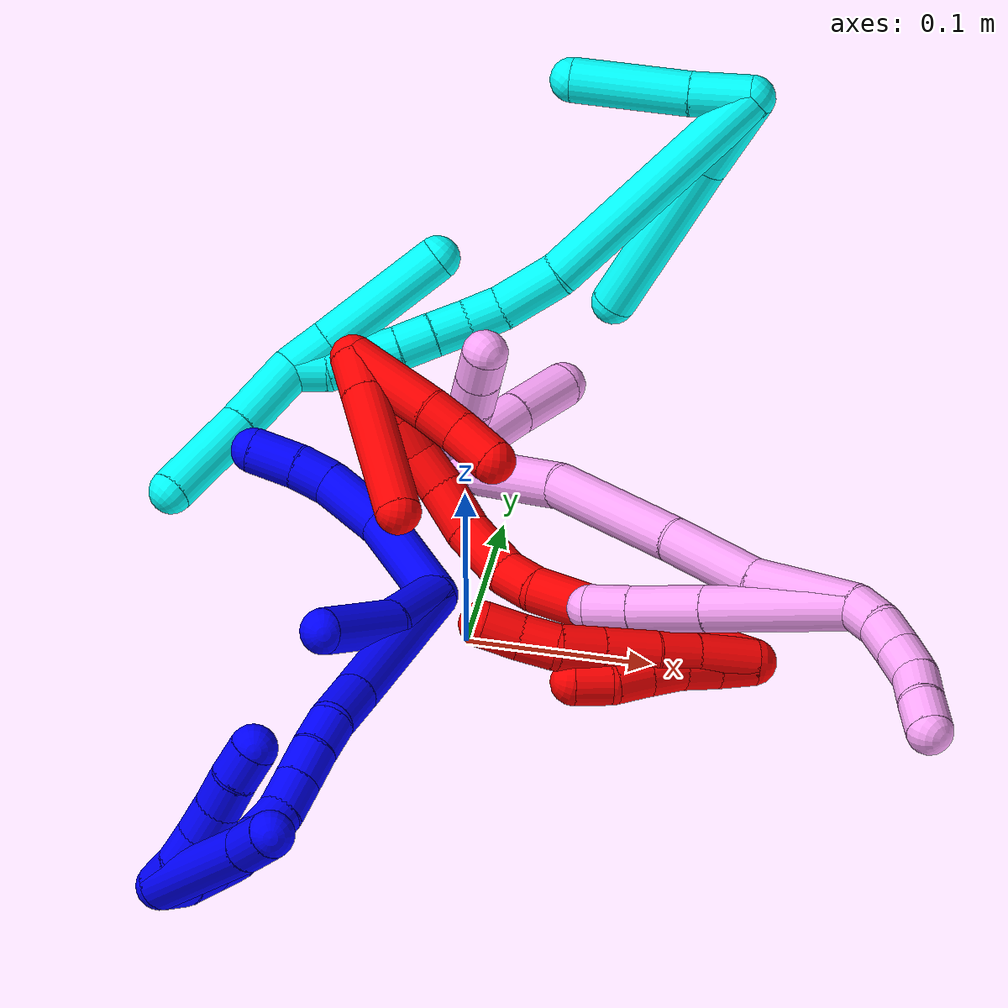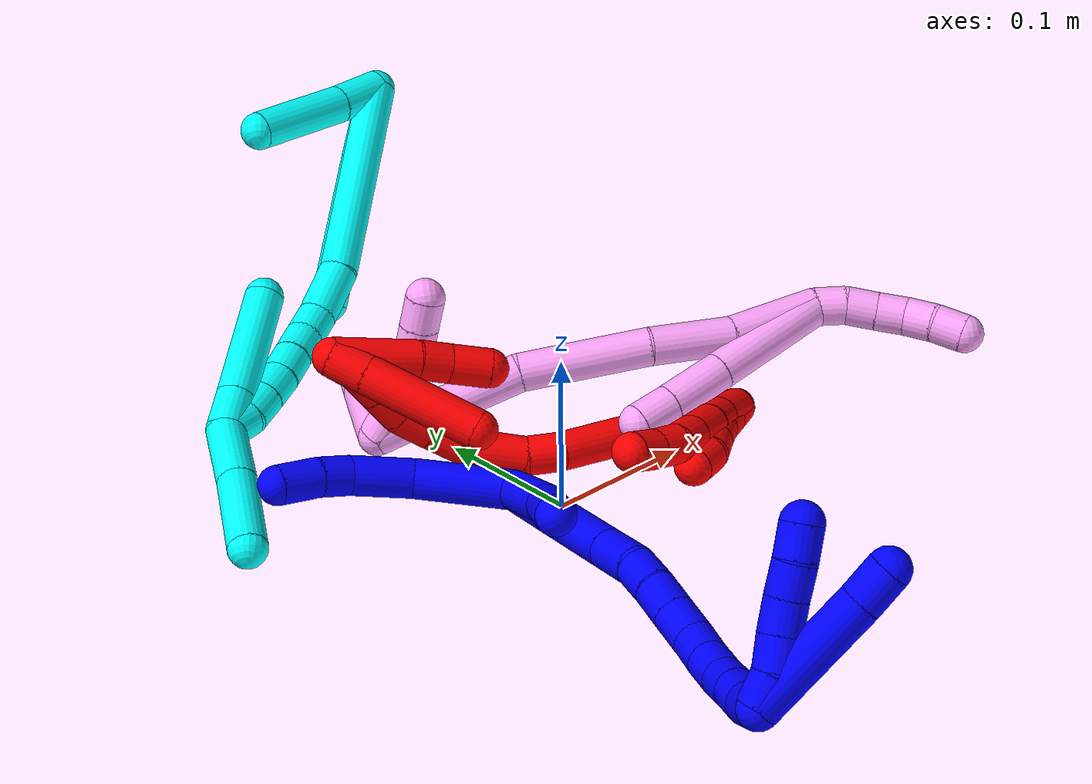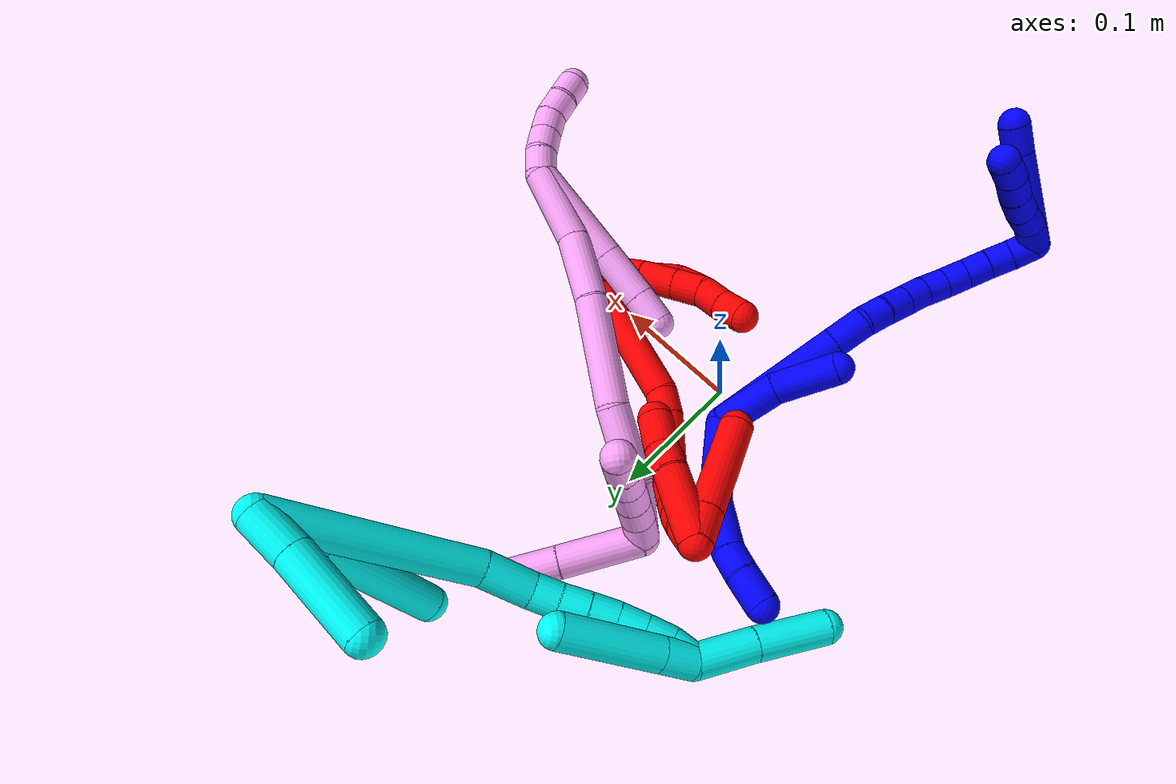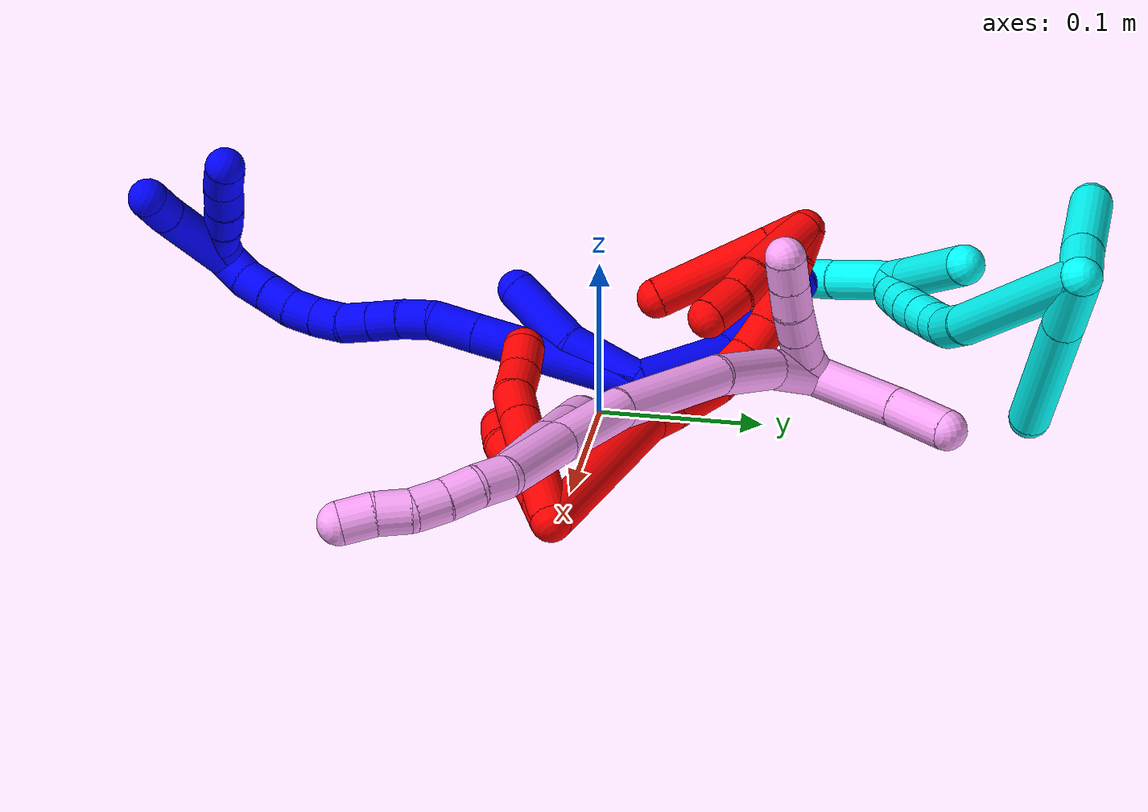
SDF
<sdf version="1.7">
 <world name="default">
  <plugin name="TubeGeneratorPlugin" filename="libtube_generator_plugin.so"/>
  <model name="photoneo_s_sensor">
   <static>1</static>
   <pose>0 0 2 1.57079 1.57079 3.14159</pose>
   <link name="link">
    <inertial><mass>0.1</mass></inertial>
    <sensor name="sensor" type="depth">
     <update_rate>30</update_rate>
     <camera>
      <horizontal_fov>1.22</horizontal_fov>
      <image><width>1920</width><height>1200</height><format>B8G8R8</format></image>
      <clip><near>0.1</near><far>4</far></clip>
      <depth_camera><output>points</output></depth_camera>
     </camera>
     <plugin name="camera_plugin" filename="libgazebo_ros_depth_camera.so">
      <baseline>0.2</baseline>
      <alwaysOn>1</alwaysOn>
      <updateRate>0.0</updateRate>
      <cameraName>camera_ir</cameraName>
      <imageTopicName>/camera/color/image_raw</imageTopicName>
      <cameraInfoTopicName>/camera/color/camera_info</cameraInfoTopicName>
      <depthImageTopicName>/camera/depth/image_raw</depthImageTopicName>
      <depthImageCameraInfoTopicName>/camera/depth/camera_info</depthImageCameraInfoTopicName>
      <pointCloudTopicName>/camera/depth/points</pointCloudTopicName>
      <frameName>fr_optical</frameName>
      <pointCloudCutoff>0.1</pointCloudCutoff>
      <pointCloudCutoffMax>2.0</pointCloudCutoffMax>
      <distortionK1>0</distortionK1>
      <distortionK2>0</distortionK2>
      <distortionK3>0</distortionK3>
      <distortionT1>0</distortionT1>
      <distortionT2>0</distortionT2>
      <CxPrime>0</CxPrime>
      <Cx>0</Cx>
      <Cy>0</Cy>
      <focalLength>0</focalLength>
      <hackBaseline>0</hackBaseline>
     </plugin>
    </sensor>
   </link>
  </model>
  <gravity>0 0 -9.8</gravity>
  <magnetic_field>6e-06 2.3e-05 -4.2e-05</magnetic_field>
  <atmosphere type="adiabatic"/>
  <physics name="default_physics" default="0" type="ode">
   <max_step_size>0.003</max_step_size>
   <real_time_factor>1</real_time_factor>
   <real_time_update_rate>1000</real_time_update_rate>
   <max_contacts>10000</max_contacts>
   <ode>
    <solver>
     <type>quick</type>
     <iters>100</iters>
     <sor>1.3</sor>
     <use_dynamic_moi_rescaling>0</use_dynamic_moi_rescaling>
    </solver>
    <constraints>
     <contact_max_correcting_vel>0</contact_max_correcting_vel>
     <contact_surface_layer>0.001</contact_surface_layer>
     <cfm>0</cfm>
     <erp>0.2</erp>
    </constraints>
   </ode>
  </physics>
  <scene><ambient>0.4 0.4 0.4 1</ambient><background>0.7 0.7 0.7 1</background><shadows>0</shadows></scene>
  <audio><device>default</device></audio>
  <spherical_coordinates>
   <surface_model>EARTH_WGS84</surface_model>
   <latitude_deg>0</latitude_deg>
   <longitude_deg>0</longitude_deg>
   <elevation>0</elevation>
   <heading_deg>0</heading_deg>
  </spherical_coordinates>
  <model name="bin">
   <static>1</static>
   <link name="bottom">
    <collision name="collision-bottom">
     <pose>0 0 -0.01 0 -0 0</pose>
     <geometry><box><size>0.8 0.6 0.02</size></box></geometry>
     <surface>
      <friction><ode><mu>100</mu><mu2>100</mu2></ode></friction>
      <contact><collide_bitmask>65535</collide_bitmask></contact>
     </surface>
    </collision>
   </link>
   <link name="west_wall">
    <collision name="collision-west_wall">
     <pose>-0.41 0 0.1 0 -0 0</pose>
     <geometry><box><size>0.02 0.6 0.2</size></box></geometry>
     <surface>
      <friction><ode><mu>100</mu><mu2>100</mu2></ode></friction>
      <contact><collide_bitmask>65535</collide_bitmask></contact>
     </surface>
    </collision>
   </link>
   <link name="east_wall">
    <collision name="collision-east_wall">
     <pose>0.41 0 0.1 0 -0 0</pose>
     <geometry><box><size>0.02 0.6 0.2</size></box></geometry>
     <surface>
      <friction><ode><mu>100</mu><mu2>100</mu2></ode></friction>
      <contact><collide_bitmask>65535</collide_bitmask></contact>
     </surface>
    </collision>
   </link>
   <link name="south_wall">
    <collision name="collision-south_wall">
     <pose>0 -0.31 0.1 0 -0 0</pose>
     <geometry><box><size>0.8 0.02 0.2</size></box></geometry>
     <surface>
      <friction><ode><mu>100</mu><mu2>100</mu2></ode></friction>
      <contact><collide_bitmask>65535</collide_bitmask></contact>
     </surface>
    </collision>
   </link>
   <link name="north_wall">
    <collision name="collision-north_wall">
     <pose>0 0.31 0.1 0 -0 0</pose>
     <geometry><box><size>0.8 0.02 0.2</size></box></geometry>
     <surface>
      <friction><ode><mu>100</mu><mu2>100</mu2></ode></friction>
      <contact><collide_bitmask>65535</collide_bitmask></contact>
     </surface>
    </collision>
   </link>
  </model>
  <model name="1">
   <static>0</static>
   <link name="1">
    <collision name="collision-cylinder-e_1_2_8">
     <pose>-0.013744 0.01539 -0.023625 -2.5642 -0.453554 1.32105</pose>
     <geometry><cylinder><radius>0.0125</radius><length>0.062734</length></cylinder></geometry>
     <surface>
      <friction><ode><mu>1.16</mu><mu2>1.16</mu2><slip1>0</slip1><slip2>0</slip2></ode></friction>
      <contact><ode><kp>1e+06</kp><kd>1</kd><max_vel>0</max_vel><min_depth>0.001</min_depth></ode></contact>
     </surface>
    </collision>
    <visual name="visual-cylinder-e_1_2_8">
     <pose>-0.013744 0.01539 -0.023625 -2.5642 -0.453554 1.32105</pose>
     <geometry><cylinder><radius>0.0125</radius><length>0.062734</length></cylinder></geometry>
     <material><ambient>0 0 1 1</ambient></material>
    </visual>
    <collision name="collision-cylinder-e_2_8_9">
     <pose>-0.0413 0.040262 -0.058264 -2.43081 -0.759963 1.64407</pose>
     <geometry><cylinder><radius>0.0125</radius><length>0.0401</length></cylinder></geometry>
     <surface>
      <friction><ode><mu>1.16</mu><mu2>1.16</mu2><slip1>0</slip1><slip2>0</slip2></ode></friction>
      <contact><ode><kp>1e+06</kp><kd>1</kd><max_vel>0</max_vel><min_depth>0.001</min_depth></ode></contact>
     </surface>
    </collision>
    <visual name="visual-cylinder-e_2_8_9">
     <pose>-0.0413 0.040262 -0.058264 -2.43081 -0.759963 1.64407</pose>
     <geometry><cylinder><radius>0.0125</radius><length>0.0401</length></cylinder></geometry>
     <material><ambient>0 0 1 1</ambient></material>
    </visual>
    <collision name="collision-cylinder-e_3_9_10">
     <pose>-0.063747 0.053569 -0.072931 -2.33311 -1.02124 1.83717</pose>
     <geometry><cylinder><radius>0.0125</radius><length>0.020252</length></cylinder></geometry>
     <surface>
      <friction><ode><mu>1.16</mu><mu2>1.16</mu2><slip1>0</slip1><slip2>0</slip2></ode></friction>
      <contact><ode><kp>1e+06</kp><kd>1</kd><max_vel>0</max_vel><min_depth>0.001</min_depth></ode></contact>
     </surface>
    </collision>
    <visual name="visual-cylinder-e_3_9_10">
     <pose>-0.063747 0.053569 -0.072931 -2.33311 -1.02124 1.83717</pose>
     <geometry><cylinder><radius>0.0125</radius><length>0.020252</length></cylinder></geometry>
     <material><ambient>0 0 1 1</ambient></material>
    </visual>
    <collision name="collision-cylinder-e_4_10_6">
     <pose>-0.084388 0.060916 -0.081539 -2.52391 -1.10203 2.18381</pose>
     <geometry><cylinder><radius>0.0125</radius><length>0.026914</length></cylinder></geometry>
     <surface>
      <friction><ode><mu>1.16</mu><mu2>1.16</mu2><slip1>0</slip1><slip2>0</slip2></ode></friction>
      <contact><ode><kp>1e+06</kp><kd>1</kd><max_vel>0</max_vel><min_depth>0.001</min_depth></ode></contact>
     </surface>
    </collision>
    <visual name="visual-cylinder-e_4_10_6">
     <pose>-0.084388 0.060916 -0.081539 -2.52391 -1.10203 2.18381</pose>
     <geometry><cylinder><radius>0.0125</radius><length>0.026914</length></cylinder></geometry>
     <material><ambient>0 0 1 1</ambient></material>
    </visual>
    <collision name="collision-cylinder-e_1_2_11">
     <pose>-0.012299 -0.004517 0.020655 0.21531 -0.526851 -0.058277</pose>
     <geometry><cylinder><radius>0.0125</radius><length>0.04892</length></cylinder></geometry>
     <surface>
      <friction><ode><mu>1.16</mu><mu2>1.16</mu2><slip1>0</slip1><slip2>0</slip2></ode></friction>
      <contact><ode><kp>1e+06</kp><kd>1</kd><max_vel>0</max_vel><min_depth>0.001</min_depth></ode></contact>
     </surface>
    </collision>
    <visual name="visual-cylinder-e_1_2_11">
     <pose>-0.012299 -0.004517 0.020655 0.21531 -0.526851 -0.058277</pose>
     <geometry><cylinder><radius>0.0125</radius><length>0.04892</length></cylinder></geometry>
     <material><ambient>0 0 1 1</ambient></material>
    </visual>
    <collision name="collision-cylinder-e_2_11_5">
     <pose>-0.0429 -0.009005 0.059123 -0.001628 -0.798928 0.000687</pose>
     <geometry><cylinder><radius>0.0125</radius><length>0.05108</length></cylinder></geometry>
     <surface>
      <friction><ode><mu>1.16</mu><mu2>1.16</mu2><slip1>0</slip1><slip2>0</slip2></ode></friction>
      <contact><ode><kp>1e+06</kp><kd>1</kd><max_vel>0</max_vel><min_depth>0.001</min_depth></ode></contact>
     </surface>
    </collision>
    <visual name="visual-cylinder-e_2_11_5">
     <pose>-0.0429 -0.009005 0.059123 -0.001628 -0.798928 0.000687</pose>
     <geometry><cylinder><radius>0.0125</radius><length>0.05108</length></cylinder></geometry>
     <material><ambient>0 0 1 1</ambient></material>
    </visual>
    <collision name="collision-cylinder-e_1_2_12">
     <pose>-0.022212 -0.020125 0.044117 0.427974 -0.429546 -0.094738</pose>
     <geometry><cylinder><radius>0.0125</radius><length>0.106671</length></cylinder></geometry>
     <surface>
      <friction><ode><mu>1.16</mu><mu2>1.16</mu2><slip1>0</slip1><slip2>0</slip2></ode></friction>
      <contact><ode><kp>1e+06</kp><kd>1</kd><max_vel>0</max_vel><min_depth>0.001</min_depth></ode></contact>
     </surface>
    </collision>
    <visual name="visual-cylinder-e_1_2_12">
     <pose>-0.022212 -0.020125 0.044117 0.427974 -0.429546 -0.094738</pose>
     <geometry><cylinder><radius>0.0125</radius><length>0.106671</length></cylinder></geometry>
     <material><ambient>0 0 1 1</ambient></material>
    </visual>
    <collision name="collision-cylinder-e_2_12_13">
     <pose>-0.050655 -0.04567 0.100474 0.416855 -0.435619 -0.09355</pose>
     <geometry><cylinder><radius>0.0125</radius><length>0.029533</length></cylinder></geometry>
     <surface>
      <friction><ode><mu>1.16</mu><mu2>1.16</mu2><slip1>0</slip1><slip2>0</slip2></ode></friction>
      <contact><ode><kp>1e+06</kp><kd>1</kd><max_vel>0</max_vel><min_depth>0.001</min_depth></ode></contact>
     </surface>
    </collision>
    <visual name="visual-cylinder-e_2_12_13">
     <pose>-0.050655 -0.04567 0.100474 0.416855 -0.435619 -0.09355</pose>
     <geometry><cylinder><radius>0.0125</radius><length>0.029533</length></cylinder></geometry>
     <material><ambient>0 0 1 1</ambient></material>
    </visual>
    <collision name="collision-cylinder-e_3_13_14">
     <pose>-0.061394 -0.057466 0.119731 0.737634 -0.443848 -0.173981</pose>
     <geometry><cylinder><radius>0.0125</radius><length>0.020996</length></cylinder></geometry>
     <surface>
      <friction><ode><mu>1.16</mu><mu2>1.16</mu2><slip1>0</slip1><slip2>0</slip2></ode></friction>
      <contact><ode><kp>1e+06</kp><kd>1</kd><max_vel>0</max_vel><min_depth>0.001</min_depth></ode></contact>
     </surface>
    </collision>
    <visual name="visual-cylinder-e_3_13_14">
     <pose>-0.061394 -0.057466 0.119731 0.737634 -0.443848 -0.173981</pose>
     <geometry><cylinder><radius>0.0125</radius><length>0.020996</length></cylinder></geometry>
     <material><ambient>0 0 1 1</ambient></material>
    </visual>
    <collision name="collision-cylinder-e_4_14_15">
     <pose>-0.070243 -0.07121 0.133047 0.863428 -0.421112 -0.196291</pose>
     <geometry><cylinder><radius>0.0125</radius><length>0.021241</length></cylinder></geometry>
     <surface>
      <friction><ode><mu>1.16</mu><mu2>1.16</mu2><slip1>0</slip1><slip2>0</slip2></ode></friction>
      <contact><ode><kp>1e+06</kp><kd>1</kd><max_vel>0</max_vel><min_depth>0.001</min_depth></ode></contact>
     </surface>
    </collision>
    <visual name="visual-cylinder-e_4_14_15">
     <pose>-0.070243 -0.07121 0.133047 0.863428 -0.421112 -0.196291</pose>
     <geometry><cylinder><radius>0.0125</radius><length>0.021241</length></cylinder></geometry>
     <material><ambient>0 0 1 1</ambient></material>
    </visual>
    <collision name="collision-cylinder-e_5_15_16">
     <pose>-0.078982 -0.085892 0.14581 0.847011 -0.423193 -0.193065</pose>
     <geometry><cylinder><radius>0.0125</radius><length>0.021412</length></cylinder></geometry>
     <surface>
      <friction><ode><mu>1.16</mu><mu2>1.16</mu2><slip1>0</slip1><slip2>0</slip2></ode></friction>
      <contact><ode><kp>1e+06</kp><kd>1</kd><max_vel>0</max_vel><min_depth>0.001</min_depth></ode></contact>
     </surface>
    </collision>
    <visual name="visual-cylinder-e_5_15_16">
     <pose>-0.078982 -0.085892 0.14581 0.847011 -0.423193 -0.193065</pose>
     <geometry><cylinder><radius>0.0125</radius><length>0.021412</length></cylinder></geometry>
     <material><ambient>0 0 1 1</ambient></material>
    </visual>
    <collision name="collision-cylinder-e_6_16_17">
     <pose>-0.089089 -0.098244 0.158824 0.65565 -0.604762 -0.211394</pose>
     <geometry><cylinder><radius>0.0125</radius><length>0.02009</length></cylinder></geometry>
     <surface>
      <friction><ode><mu>1.16</mu><mu2>1.16</mu2><slip1>0</slip1><slip2>0</slip2></ode></friction>
      <contact><ode><kp>1e+06</kp><kd>1</kd><max_vel>0</max_vel><min_depth>0.001</min_depth></ode></contact>
     </surface>
    </collision>
    <visual name="visual-cylinder-e_6_16_17">
     <pose>-0.089089 -0.098244 0.158824 0.65565 -0.604762 -0.211394</pose>
     <geometry><cylinder><radius>0.0125</radius><length>0.02009</length></cylinder></geometry>
     <material><ambient>0 0 1 1</ambient></material>
    </visual>
    <collision name="collision-cylinder-e_7_17_18">
     <pose>-0.100634 -0.107338 0.172439 0.521148 -0.621449 -0.170831</pose>
     <geometry><cylinder><radius>0.0125</radius><length>0.020038</length></cylinder></geometry>
     <surface>
      <friction><ode><mu>1.16</mu><mu2>1.16</mu2><slip1>0</slip1><slip2>0</slip2></ode></friction>
      <contact><ode><kp>1e+06</kp><kd>1</kd><max_vel>0</max_vel><min_depth>0.001</min_depth></ode></contact>
     </surface>
    </collision>
    <visual name="visual-cylinder-e_7_17_18">
     <pose>-0.100634 -0.107338 0.172439 0.521148 -0.621449 -0.170831</pose>
     <geometry><cylinder><radius>0.0125</radius><length>0.020038</length></cylinder></geometry>
     <material><ambient>0 0 1 1</ambient></material>
    </visual>
    <collision name="collision-cylinder-e_8_18_19">
     <pose>-0.11274 -0.113318 0.187056 0.249557 -0.677697 -0.088356</pose>
     <geometry><cylinder><radius>0.0125</radius><length>0.02001</length></cylinder></geometry>
     <surface>
      <friction><ode><mu>1.16</mu><mu2>1.16</mu2><slip1>0</slip1><slip2>0</slip2></ode></friction>
      <contact><ode><kp>1e+06</kp><kd>1</kd><max_vel>0</max_vel><min_depth>0.001</min_depth></ode></contact>
     </surface>
    </collision>
    <visual name="visual-cylinder-e_8_18_19">
     <pose>-0.11274 -0.113318 0.187056 0.249557 -0.677697 -0.088356</pose>
     <geometry><cylinder><radius>0.0125</radius><length>0.02001</length></cylinder></geometry>
     <material><ambient>0 0 1 1</ambient></material>
    </visual>
    <collision name="collision-cylinder-e_9_19_20">
     <pose>-0.125511 -0.117426 0.201891 0.291185 -0.707163 -0.108135</pose>
     <geometry><cylinder><radius>0.0125</radius><length>0.020002</length></cylinder></geometry>
     <surface>
      <friction><ode><mu>1.16</mu><mu2>1.16</mu2><slip1>0</slip1><slip2>0</slip2></ode></friction>
      <contact><ode><kp>1e+06</kp><kd>1</kd><max_vel>0</max_vel><min_depth>0.001</min_depth></ode></contact>
     </surface>
    </collision>
    <visual name="visual-cylinder-e_9_19_20">
     <pose>-0.125511 -0.117426 0.201891 0.291185 -0.707163 -0.108135</pose>
     <geometry><cylinder><radius>0.0125</radius><length>0.020002</length></cylinder></geometry>
     <material><ambient>0 0 1 1</ambient></material>
    </visual>
    <collision name="collision-cylinder-e_10_20_1">
     <pose>-0.138369 -0.119261 0.216887 -0.044993 -0.689124 0.016149</pose>
     <geometry><cylinder><radius>0.0125</radius><length>0.020007</length></cylinder></geometry>
     <surface>
      <friction><ode><mu>1.16</mu><mu2>1.16</mu2><slip1>0</slip1><slip2>0</slip2></ode></friction>
      <contact><ode><kp>1e+06</kp><kd>1</kd><max_vel>0</max_vel><min_depth>0.001</min_depth></ode></contact>
     </surface>
    </collision>
    <visual name="visual-cylinder-e_10_20_1">
     <pose>-0.138369 -0.119261 0.216887 -0.044993 -0.689124 0.016149</pose>
     <geometry><cylinder><radius>0.0125</radius><length>0.020007</length></cylinder></geometry>
     <material><ambient>0 0 1 1</ambient></material>
    </visual>
    <collision name="collision-cylinder-e_1_1_21">
     <pose>-0.13983 -0.112357 0.230344 -0.851418 0.512086 -0.236304</pose>
     <geometry><cylinder><radius>0.0125</radius><length>0.02</length></cylinder></geometry>
     <surface>
      <friction><ode><mu>1.16</mu><mu2>1.16</mu2><slip1>0</slip1><slip2>0</slip2></ode></friction>
      <contact><ode><kp>1e+06</kp><kd>1</kd><max_vel>0</max_vel><min_depth>0.001</min_depth></ode></contact>
     </surface>
    </collision>
    <visual name="visual-cylinder-e_1_1_21">
     <pose>-0.13983 -0.112357 0.230344 -0.851418 0.512086 -0.236304</pose>
     <geometry><cylinder><radius>0.0125</radius><length>0.02</length></cylinder></geometry>
     <material><ambient>0 0 1 1</ambient></material>
    </visual>
    <collision name="collision-cylinder-e_2_21_22">
     <pose>-0.13006 -0.097547 0.238948 -1.23718 0.50864 -0.365917</pose>
     <geometry><cylinder><radius>0.0125</radius><length>0.02</length></cylinder></geometry>
     <surface>
      <friction><ode><mu>1.16</mu><mu2>1.16</mu2><slip1>0</slip1><slip2>0</slip2></ode></friction>
      <contact><ode><kp>1e+06</kp><kd>1</kd><max_vel>0</max_vel><min_depth>0.001</min_depth></ode></contact>
     </surface>
    </collision>
    <visual name="visual-cylinder-e_2_21_22">
     <pose>-0.13006 -0.097547 0.238948 -1.23718 0.50864 -0.365917</pose>
     <geometry><cylinder><radius>0.0125</radius><length>0.02</length></cylinder></geometry>
     <material><ambient>0 0 1 1</ambient></material>
    </visual>
    <collision name="collision-cylinder-e_3_22_23">
     <pose>-0.120867 -0.081127 0.245629 -1.13316 0.447075 -0.287251</pose>
     <geometry><cylinder><radius>0.0125</radius><length>0.02</length></cylinder></geometry>
     <surface>
      <friction><ode><mu>1.16</mu><mu2>1.16</mu2><slip1>0</slip1><slip2>0</slip2></ode></friction>
      <contact><ode><kp>1e+06</kp><kd>1</kd><max_vel>0</max_vel><min_depth>0.001</min_depth></ode></contact>
     </surface>
    </collision>
    <visual name="visual-cylinder-e_3_22_23">
     <pose>-0.120867 -0.081127 0.245629 -1.13316 0.447075 -0.287251</pose>
     <geometry><cylinder><radius>0.0125</radius><length>0.02</length></cylinder></geometry>
     <material><ambient>0 0 1 1</ambient></material>
    </visual>
    <collision name="collision-cylinder-e_4_23_24">
     <pose>-0.112856 -0.064922 0.25412 -1.04454 0.377687 -0.219129</pose>
     <geometry><cylinder><radius>0.0125</radius><length>0.02</length></cylinder></geometry>
     <surface>
      <friction><ode><mu>1.16</mu><mu2>1.16</mu2><slip1>0</slip1><slip2>0</slip2></ode></friction>
      <contact><ode><kp>1e+06</kp><kd>1</kd><max_vel>0</max_vel><min_depth>0.001</min_depth></ode></contact>
     </surface>
    </collision>
    <visual name="visual-cylinder-e_4_23_24">
     <pose>-0.112856 -0.064922 0.25412 -1.04454 0.377687 -0.219129</pose>
     <geometry><cylinder><radius>0.0125</radius><length>0.02</length></cylinder></geometry>
     <material><ambient>0 0 1 1</ambient></material>
    </visual>
    <collision name="collision-cylinder-e_5_24_4">
     <pose>-0.104659 -0.048707 0.262365 -1.15852 0.467745 -0.309174</pose>
     <geometry><cylinder><radius>0.0125</radius><length>0.02</length></cylinder></geometry>
     <surface>
      <friction><ode><mu>1.16</mu><mu2>1.16</mu2><slip1>0</slip1><slip2>0</slip2></ode></friction>
      <contact><ode><kp>1e+06</kp><kd>1</kd><max_vel>0</max_vel><min_depth>0.001</min_depth></ode></contact>
     </surface>
    </collision>
    <visual name="visual-cylinder-e_5_24_4">
     <pose>-0.104659 -0.048707 0.262365 -1.15852 0.467745 -0.309174</pose>
     <geometry><cylinder><radius>0.0125</radius><length>0.02</length></cylinder></geometry>
     <material><ambient>0 0 1 1</ambient></material>
    </visual>
    <collision name="collision-cylinder-e_1_1_25">
     <pose>-0.123845 -0.103707 0.25329 -0.48739 0.571583 -0.145857</pose>
     <geometry><cylinder><radius>0.0125</radius><length>0.077215</length></cylinder></geometry>
     <surface>
      <friction><ode><mu>1.16</mu><mu2>1.16</mu2><slip1>0</slip1><slip2>0</slip2></ode></friction>
      <contact><ode><kp>1e+06</kp><kd>1</kd><max_vel>0</max_vel><min_depth>0.001</min_depth></ode></contact>
     </surface>
    </collision>
    <visual name="visual-cylinder-e_1_1_25">
     <pose>-0.123845 -0.103707 0.25329 -0.48739 0.571583 -0.145857</pose>
     <geometry><cylinder><radius>0.0125</radius><length>0.077215</length></cylinder></geometry>
     <material><ambient>0 0 1 1</ambient></material>
    </visual>
    <collision name="collision-cylinder-e_2_25_3">
     <pose>-0.097186 -0.083448 0.290401 -0.540414 0.531416 -0.150472</pose>
     <geometry><cylinder><radius>0.0125</radius><length>0.022785</length></cylinder></geometry>
     <surface>
      <friction><ode><mu>1.16</mu><mu2>1.16</mu2><slip1>0</slip1><slip2>0</slip2></ode></friction>
      <contact><ode><kp>1e+06</kp><kd>1</kd><max_vel>0</max_vel><min_depth>0.001</min_depth></ode></contact>
     </surface>
    </collision>
    <visual name="visual-cylinder-e_2_25_3">
     <pose>-0.097186 -0.083448 0.290401 -0.540414 0.531416 -0.150472</pose>
     <geometry><cylinder><radius>0.0125</radius><length>0.022785</length></cylinder></geometry>
     <material><ambient>0 0 1 1</ambient></material>
    </visual>
    <collision name="collision-sphere-3">
     <pose>-0.091413 -0.078395 0.298823 0 -0 0</pose>
     <geometry><sphere><radius>0.0125</radius></sphere></geometry>
     <surface>
      <friction><ode><mu>1.16</mu><mu2>1.16</mu2><slip1>0</slip1><slip2>0</slip2></ode></friction>
      <contact><ode><kp>1e+06</kp><kd>1</kd><max_vel>0</max_vel><min_depth>0.001</min_depth></ode></contact>
     </surface>
    </collision>
    <visual name="visual-sphere-3">
     <pose>-0.091413 -0.078395 0.298823 0 -0 0</pose>
     <geometry><sphere><radius>0.0125</radius></sphere></geometry>
     <material><ambient>0 0 1 1</ambient></material>
    </visual>
    <collision name="collision-sphere-25">
     <pose>-0.102959 -0.0885 0.281979 0 -0 0</pose>
     <geometry><sphere><radius>0.0125</radius></sphere></geometry>
     <surface>
      <friction><ode><mu>1.16</mu><mu2>1.16</mu2><slip1>0</slip1><slip2>0</slip2></ode></friction>
      <contact><ode><kp>1e+06</kp><kd>1</kd><max_vel>0</max_vel><min_depth>0.001</min_depth></ode></contact>
     </surface>
    </collision>
    <visual name="visual-sphere-25">
     <pose>-0.102959 -0.0885 0.281979 0 -0 0</pose>
     <geometry><sphere><radius>0.0125</radius></sphere></geometry>
     <material><ambient>0 0 1 1</ambient></material>
    </visual>
    <collision name="collision-sphere-4">
     <pose>-0.100151 -0.040529 0.265942 0 -0 0</pose>
     <geometry><sphere><radius>0.0125</radius></sphere></geometry>
     <surface>
      <friction><ode><mu>1.16</mu><mu2>1.16</mu2><slip1>0</slip1><slip2>0</slip2></ode></friction>
      <contact><ode><kp>1e+06</kp><kd>1</kd><max_vel>0</max_vel><min_depth>0.001</min_depth></ode></contact>
     </surface>
    </collision>
    <visual name="visual-sphere-4">
     <pose>-0.100151 -0.040529 0.265942 0 -0 0</pose>
     <geometry><sphere><radius>0.0125</radius></sphere></geometry>
     <material><ambient>0 0 1 1</ambient></material>
    </visual>
    <collision name="collision-sphere-24">
     <pose>-0.109168 -0.056885 0.258789 0 -0 0</pose>
     <geometry><sphere><radius>0.0125</radius></sphere></geometry>
     <surface>
      <friction><ode><mu>1.16</mu><mu2>1.16</mu2><slip1>0</slip1><slip2>0</slip2></ode></friction>
      <contact><ode><kp>1e+06</kp><kd>1</kd><max_vel>0</max_vel><min_depth>0.001</min_depth></ode></contact>
     </surface>
    </collision>
    <visual name="visual-sphere-24">
     <pose>-0.109168 -0.056885 0.258789 0 -0 0</pose>
     <geometry><sphere><radius>0.0125</radius></sphere></geometry>
     <material><ambient>0 0 1 1</ambient></material>
    </visual>
    <collision name="collision-sphere-23">
     <pose>-0.116544 -0.07296 0.249451 0 -0 0</pose>
     <geometry><sphere><radius>0.0125</radius></sphere></geometry>
     <surface>
      <friction><ode><mu>1.16</mu><mu2>1.16</mu2><slip1>0</slip1><slip2>0</slip2></ode></friction>
      <contact><ode><kp>1e+06</kp><kd>1</kd><max_vel>0</max_vel><min_depth>0.001</min_depth></ode></contact>
     </surface>
    </collision>
    <visual name="visual-sphere-23">
     <pose>-0.116544 -0.07296 0.249451 0 -0 0</pose>
     <geometry><sphere><radius>0.0125</radius></sphere></geometry>
     <material><ambient>0 0 1 1</ambient></material>
    </visual>
    <collision name="collision-sphere-22">
     <pose>-0.12519 -0.089295 0.241808 0 -0 0</pose>
     <geometry><sphere><radius>0.0125</radius></sphere></geometry>
     <surface>
      <friction><ode><mu>1.16</mu><mu2>1.16</mu2><slip1>0</slip1><slip2>0</slip2></ode></friction>
      <contact><ode><kp>1e+06</kp><kd>1</kd><max_vel>0</max_vel><min_depth>0.001</min_depth></ode></contact>
     </surface>
    </collision>
    <visual name="visual-sphere-22">
     <pose>-0.12519 -0.089295 0.241808 0 -0 0</pose>
     <geometry><sphere><radius>0.0125</radius></sphere></geometry>
     <material><ambient>0 0 1 1</ambient></material>
    </visual>
    <collision name="collision-sphere-21">
     <pose>-0.13493 -0.1058 0.236088 0 -0 0</pose>
     <geometry><sphere><radius>0.0125</radius></sphere></geometry>
     <surface>
      <friction><ode><mu>1.16</mu><mu2>1.16</mu2><slip1>0</slip1><slip2>0</slip2></ode></friction>
      <contact><ode><kp>1e+06</kp><kd>1</kd><max_vel>0</max_vel><min_depth>0.001</min_depth></ode></contact>
     </surface>
    </collision>
    <visual name="visual-sphere-21">
     <pose>-0.13493 -0.1058 0.236088 0 -0 0</pose>
     <geometry><sphere><radius>0.0125</radius></sphere></geometry>
     <material><ambient>0 0 1 1</ambient></material>
    </visual>
    <collision name="collision-sphere-1">
     <pose>-0.14473 -0.118914 0.2246 0 -0 0</pose>
     <geometry><sphere><radius>0.0125</radius></sphere></geometry>
     <surface>
      <friction><ode><mu>1.16</mu><mu2>1.16</mu2><slip1>0</slip1><slip2>0</slip2></ode></friction>
      <contact><ode><kp>1e+06</kp><kd>1</kd><max_vel>0</max_vel><min_depth>0.001</min_depth></ode></contact>
     </surface>
    </collision>
    <visual name="visual-sphere-1">
     <pose>-0.14473 -0.118914 0.2246 0 -0 0</pose>
     <geometry><sphere><radius>0.0125</radius></sphere></geometry>
     <material><ambient>0 0 1 1</ambient></material>
    </visual>
    <collision name="collision-sphere-11">
     <pose>-0.024597 -0.009034 0.041309 0 -0 0</pose>
     <geometry><sphere><radius>0.0125</radius></sphere></geometry>
     <surface>
      <friction><ode><mu>1.16</mu><mu2>1.16</mu2><slip1>0</slip1><slip2>0</slip2></ode></friction>
      <contact><ode><kp>1e+06</kp><kd>1</kd><max_vel>0</max_vel><min_depth>0.001</min_depth></ode></contact>
     </surface>
    </collision>
    <visual name="visual-sphere-11">
     <pose>-0.024597 -0.009034 0.041309 0 -0 0</pose>
     <geometry><sphere><radius>0.0125</radius></sphere></geometry>
     <material><ambient>0 0 1 1</ambient></material>
    </visual>
    <collision name="collision-sphere-6">
     <pose>-0.096393 0.064437 -0.086496 0 -0 0</pose>
     <geometry><sphere><radius>0.0125</radius></sphere></geometry>
     <surface>
      <friction><ode><mu>1.16</mu><mu2>1.16</mu2><slip1>0</slip1><slip2>0</slip2></ode></friction>
      <contact><ode><kp>1e+06</kp><kd>1</kd><max_vel>0</max_vel><min_depth>0.001</min_depth></ode></contact>
     </surface>
    </collision>
    <visual name="visual-sphere-6">
     <pose>-0.096393 0.064437 -0.086496 0 -0 0</pose>
     <geometry><sphere><radius>0.0125</radius></sphere></geometry>
     <material><ambient>0 0 1 1</ambient></material>
    </visual>
    <collision name="collision-sphere-10">
     <pose>-0.072382 0.057395 -0.076583 0 -0 0</pose>
     <geometry><sphere><radius>0.0125</radius></sphere></geometry>
     <surface>
      <friction><ode><mu>1.16</mu><mu2>1.16</mu2><slip1>0</slip1><slip2>0</slip2></ode></friction>
      <contact><ode><kp>1e+06</kp><kd>1</kd><max_vel>0</max_vel><min_depth>0.001</min_depth></ode></contact>
     </surface>
    </collision>
    <visual name="visual-sphere-10">
     <pose>-0.072382 0.057395 -0.076583 0 -0 0</pose>
     <geometry><sphere><radius>0.0125</radius></sphere></geometry>
     <material><ambient>0 0 1 1</ambient></material>
    </visual>
    <collision name="collision-sphere-9">
     <pose>-0.055112 0.049744 -0.069278 0 -0 0</pose>
     <geometry><sphere><radius>0.0125</radius></sphere></geometry>
     <surface>
      <friction><ode><mu>1.16</mu><mu2>1.16</mu2><slip1>0</slip1><slip2>0</slip2></ode></friction>
      <contact><ode><kp>1e+06</kp><kd>1</kd><max_vel>0</max_vel><min_depth>0.001</min_depth></ode></contact>
     </surface>
    </collision>
    <visual name="visual-sphere-9">
     <pose>-0.055112 0.049744 -0.069278 0 -0 0</pose>
     <geometry><sphere><radius>0.0125</radius></sphere></geometry>
     <material><ambient>0 0 1 1</ambient></material>
    </visual>
    <collision name="collision-sphere-2">
     <geometry><sphere><radius>0.0125</radius></sphere></geometry>
     <surface>
      <friction><ode><mu>1.16</mu><mu2>1.16</mu2><slip1>0</slip1><slip2>0</slip2></ode></friction>
      <contact><ode><kp>1e+06</kp><kd>1</kd><max_vel>0</max_vel><min_depth>0.001</min_depth></ode></contact>
     </surface>
    </collision>
    <visual name="visual-sphere-2">
     <geometry><sphere><radius>0.0125</radius></sphere></geometry>
     <material><ambient>0 0 1 1</ambient></material>
    </visual>
    <collision name="collision-sphere-19">
     <pose>-0.119014 -0.115243 0.194609 0 -0 0</pose>
     <geometry><sphere><radius>0.0125</radius></sphere></geometry>
     <surface>
      <friction><ode><mu>1.16</mu><mu2>1.16</mu2><slip1>0</slip1><slip2>0</slip2></ode></friction>
      <contact><ode><kp>1e+06</kp><kd>1</kd><max_vel>0</max_vel><min_depth>0.001</min_depth></ode></contact>
     </surface>
    </collision>
    <visual name="visual-sphere-19">
     <pose>-0.119014 -0.115243 0.194609 0 -0 0</pose>
     <geometry><sphere><radius>0.0125</radius></sphere></geometry>
     <material><ambient>0 0 1 1</ambient></material>
    </visual>
    <collision name="collision-sphere-8">
     <pose>-0.027488 0.03078 -0.04725 0 -0 0</pose>
     <geometry><sphere><radius>0.0125</radius></sphere></geometry>
     <surface>
      <friction><ode><mu>1.16</mu><mu2>1.16</mu2><slip1>0</slip1><slip2>0</slip2></ode></friction>
      <contact><ode><kp>1e+06</kp><kd>1</kd><max_vel>0</max_vel><min_depth>0.001</min_depth></ode></contact>
     </surface>
    </collision>
    <visual name="visual-sphere-8">
     <pose>-0.027488 0.03078 -0.04725 0 -0 0</pose>
     <geometry><sphere><radius>0.0125</radius></sphere></geometry>
     <material><ambient>0 0 1 1</ambient></material>
    </visual>
    <collision name="collision-sphere-5">
     <pose>-0.061202 -0.008976 0.076937 0 -0 0</pose>
     <geometry><sphere><radius>0.0125</radius></sphere></geometry>
     <surface>
      <friction><ode><mu>1.16</mu><mu2>1.16</mu2><slip1>0</slip1><slip2>0</slip2></ode></friction>
      <contact><ode><kp>1e+06</kp><kd>1</kd><max_vel>0</max_vel><min_depth>0.001</min_depth></ode></contact>
     </surface>
    </collision>
    <visual name="visual-sphere-5">
     <pose>-0.061202 -0.008976 0.076937 0 -0 0</pose>
     <geometry><sphere><radius>0.0125</radius></sphere></geometry>
     <material><ambient>0 0 1 1</ambient></material>
    </visual>
    <collision name="collision-sphere-12">
     <pose>-0.044424 -0.040249 0.088233 0 -0 0</pose>
     <geometry><sphere><radius>0.0125</radius></sphere></geometry>
     <surface>
      <friction><ode><mu>1.16</mu><mu2>1.16</mu2><slip1>0</slip1><slip2>0</slip2></ode></friction>
      <contact><ode><kp>1e+06</kp><kd>1</kd><max_vel>0</max_vel><min_depth>0.001</min_depth></ode></contact>
     </surface>
    </collision>
    <visual name="visual-sphere-12">
     <pose>-0.044424 -0.040249 0.088233 0 -0 0</pose>
     <geometry><sphere><radius>0.0125</radius></sphere></geometry>
     <material><ambient>0 0 1 1</ambient></material>
    </visual>
    <collision name="collision-sphere-13">
     <pose>-0.056886 -0.05109 0.112715 0 -0 0</pose>
     <geometry><sphere><radius>0.0125</radius></sphere></geometry>
     <surface>
      <friction><ode><mu>1.16</mu><mu2>1.16</mu2><slip1>0</slip1><slip2>0</slip2></ode></friction>
      <contact><ode><kp>1e+06</kp><kd>1</kd><max_vel>0</max_vel><min_depth>0.001</min_depth></ode></contact>
     </surface>
    </collision>
    <visual name="visual-sphere-13">
     <pose>-0.056886 -0.05109 0.112715 0 -0 0</pose>
     <geometry><sphere><radius>0.0125</radius></sphere></geometry>
     <material><ambient>0 0 1 1</ambient></material>
    </visual>
    <collision name="collision-sphere-14">
     <pose>-0.065902 -0.063843 0.126748 0 -0 0</pose>
     <geometry><sphere><radius>0.0125</radius></sphere></geometry>
     <surface>
      <friction><ode><mu>1.16</mu><mu2>1.16</mu2><slip1>0</slip1><slip2>0</slip2></ode></friction>
      <contact><ode><kp>1e+06</kp><kd>1</kd><max_vel>0</max_vel><min_depth>0.001</min_depth></ode></contact>
     </surface>
    </collision>
    <visual name="visual-sphere-14">
     <pose>-0.065902 -0.063843 0.126748 0 -0 0</pose>
     <geometry><sphere><radius>0.0125</radius></sphere></geometry>
     <material><ambient>0 0 1 1</ambient></material>
    </visual>
    <collision name="collision-sphere-15">
     <pose>-0.074585 -0.078577 0.139345 0 -0 0</pose>
     <geometry><sphere><radius>0.0125</radius></sphere></geometry>
     <surface>
      <friction><ode><mu>1.16</mu><mu2>1.16</mu2><slip1>0</slip1><slip2>0</slip2></ode></friction>
      <contact><ode><kp>1e+06</kp><kd>1</kd><max_vel>0</max_vel><min_depth>0.001</min_depth></ode></contact>
     </surface>
    </collision>
    <visual name="visual-sphere-15">
     <pose>-0.074585 -0.078577 0.139345 0 -0 0</pose>
     <geometry><sphere><radius>0.0125</radius></sphere></geometry>
     <material><ambient>0 0 1 1</ambient></material>
    </visual>
    <collision name="collision-sphere-16">
     <pose>-0.083378 -0.093206 0.152274 0 -0 0</pose>
     <geometry><sphere><radius>0.0125</radius></sphere></geometry>
     <surface>
      <friction><ode><mu>1.16</mu><mu2>1.16</mu2><slip1>0</slip1><slip2>0</slip2></ode></friction>
      <contact><ode><kp>1e+06</kp><kd>1</kd><max_vel>0</max_vel><min_depth>0.001</min_depth></ode></contact>
     </surface>
    </collision>
    <visual name="visual-sphere-16">
     <pose>-0.083378 -0.093206 0.152274 0 -0 0</pose>
     <geometry><sphere><radius>0.0125</radius></sphere></geometry>
     <material><ambient>0 0 1 1</ambient></material>
    </visual>
    <collision name="collision-sphere-17">
     <pose>-0.094801 -0.103282 0.165374 0 -0 0</pose>
     <geometry><sphere><radius>0.0125</radius></sphere></geometry>
     <surface>
      <friction><ode><mu>1.16</mu><mu2>1.16</mu2><slip1>0</slip1><slip2>0</slip2></ode></friction>
      <contact><ode><kp>1e+06</kp><kd>1</kd><max_vel>0</max_vel><min_depth>0.001</min_depth></ode></contact>
     </surface>
    </collision>
    <visual name="visual-sphere-17">
     <pose>-0.094801 -0.103282 0.165374 0 -0 0</pose>
     <geometry><sphere><radius>0.0125</radius></sphere></geometry>
     <material><ambient>0 0 1 1</ambient></material>
    </visual>
    <collision name="collision-sphere-18">
     <pose>-0.106467 -0.111393 0.179503 0 -0 0</pose>
     <geometry><sphere><radius>0.0125</radius></sphere></geometry>
     <surface>
      <friction><ode><mu>1.16</mu><mu2>1.16</mu2><slip1>0</slip1><slip2>0</slip2></ode></friction>
      <contact><ode><kp>1e+06</kp><kd>1</kd><max_vel>0</max_vel><min_depth>0.001</min_depth></ode></contact>
     </surface>
    </collision>
    <visual name="visual-sphere-18">
     <pose>-0.106467 -0.111393 0.179503 0 -0 0</pose>
     <geometry><sphere><radius>0.0125</radius></sphere></geometry>
     <material><ambient>0 0 1 1</ambient></material>
    </visual>
    <collision name="collision-sphere-20">
     <pose>-0.132009 -0.119609 0.209174 0 -0 0</pose>
     <geometry><sphere><radius>0.0125</radius></sphere></geometry>
     <surface>
      <friction><ode><mu>1.16</mu><mu2>1.16</mu2><slip1>0</slip1><slip2>0</slip2></ode></friction>
      <contact><ode><kp>1e+06</kp><kd>1</kd><max_vel>0</max_vel><min_depth>0.001</min_depth></ode></contact>
     </surface>
    </collision>
    <visual name="visual-sphere-20">
     <pose>-0.132009 -0.119609 0.209174 0 -0 0</pose>
     <geometry><sphere><radius>0.0125</radius></sphere></geometry>
     <material><ambient>0 0 1 1</ambient></material>
    </visual>
    <inertial>
     <pose>-0.069993 -0.043413 0.10966 0 -0 0</pose>
     <mass>0.75</mass>
     <inertia>
      <ixx>0.000166</ixx>
      <ixy>0</ixy>
      <ixz>0</ixz>
      <iyy>0.000199</iyy>
      <iyz>0</iyz>
      <izz>9.4e-05</izz>
     </inertia>
    </inertial>
   </link>
   <pose>-0.021265 0.020174 0.011545 1.03288 0.051841 0.225125</pose>
  </model>
  <model name="2">
   <static>0</static>
   <link name="2">
    <collision name="collision-cylinder-e_1_2_8">
     <pose>0.000158 -0.000125 -0.016554 3.13407 0.009549 1.80724</pose>
     <geometry><cylinder><radius>0.0125</radius><length>0.03311</length></cylinder></geometry>
     <surface>
      <friction><ode><mu>1.16</mu><mu2>1.16</mu2><slip1>0</slip1><slip2>0</slip2></ode></friction>
      <contact><ode><kp>1e+06</kp><kd>1</kd><max_vel>0</max_vel><min_depth>0.001</min_depth></ode></contact>
     </surface>
    </collision>
    <visual name="visual-cylinder-e_1_2_8">
     <pose>0.000158 -0.000125 -0.016554 3.13407 0.009549 1.80724</pose>
     <geometry><cylinder><radius>0.0125</radius><length>0.03311</length></cylinder></geometry>
     <material><ambient>1 0 0 1</ambient></material>
    </visual>
    <collision name="collision-cylinder-e_2_8_9">
     <pose>0.000724 -0.0009 -0.044184 3.08288 0.036744 1.1182</pose>
     <geometry><cylinder><radius>0.0125</radius><length>0.022206</length></cylinder></geometry>
     <surface>
      <friction><ode><mu>1.16</mu><mu2>1.16</mu2><slip1>0</slip1><slip2>0</slip2></ode></friction>
      <contact><ode><kp>1e+06</kp><kd>1</kd><max_vel>0</max_vel><min_depth>0.001</min_depth></ode></contact>
     </surface>
    </collision>
    <visual name="visual-cylinder-e_2_8_9">
     <pose>0.000724 -0.0009 -0.044184 3.08288 0.036744 1.1182</pose>
     <geometry><cylinder><radius>0.0125</radius><length>0.022206</length></cylinder></geometry>
     <material><ambient>1 0 0 1</ambient></material>
    </visual>
    <collision name="collision-cylinder-e_3_9_10">
     <pose>0.001995 -0.000883 -0.07012 -3.09663 0.057932 -1.82175</pose>
     <geometry><cylinder><radius>0.0125</radius><length>0.0298</length></cylinder></geometry>
     <surface>
      <friction><ode><mu>1.16</mu><mu2>1.16</mu2><slip1>0</slip1><slip2>0</slip2></ode></friction>
      <contact><ode><kp>1e+06</kp><kd>1</kd><max_vel>0</max_vel><min_depth>0.001</min_depth></ode></contact>
     </surface>
    </collision>
    <visual name="visual-cylinder-e_3_9_10">
     <pose>0.001995 -0.000883 -0.07012 -3.09663 0.057932 -1.82175</pose>
     <geometry><cylinder><radius>0.0125</radius><length>0.0298</length></cylinder></geometry>
     <material><ambient>1 0 0 1</ambient></material>
    </visual>
    <collision name="collision-cylinder-e_4_10_11">
     <pose>0.003496 0.000408 -0.096763 -3.08883 0.054094 -1.5958</pose>
     <geometry><cylinder><radius>0.0125</radius><length>0.023633</length></cylinder></geometry>
     <surface>
      <friction><ode><mu>1.16</mu><mu2>1.16</mu2><slip1>0</slip1><slip2>0</slip2></ode></friction>
      <contact><ode><kp>1e+06</kp><kd>1</kd><max_vel>0</max_vel><min_depth>0.001</min_depth></ode></contact>
     </surface>
    </collision>
    <visual name="visual-cylinder-e_4_10_11">
     <pose>0.003496 0.000408 -0.096763 -3.08883 0.054094 -1.5958</pose>
     <geometry><cylinder><radius>0.0125</radius><length>0.023633</length></cylinder></geometry>
     <material><ambient>1 0 0 1</ambient></material>
    </visual>
    <collision name="collision-cylinder-e_5_11_12">
     <pose>0.003611 0.00478 -0.117932 -2.76152 -0.051816 0.267817</pose>
     <geometry><cylinder><radius>0.0125</radius><length>0.020243</length></cylinder></geometry>
     <surface>
      <friction><ode><mu>1.16</mu><mu2>1.16</mu2><slip1>0</slip1><slip2>0</slip2></ode></friction>
      <contact><ode><kp>1e+06</kp><kd>1</kd><max_vel>0</max_vel><min_depth>0.001</min_depth></ode></contact>
     </surface>
    </collision>
    <visual name="visual-cylinder-e_5_11_12">
     <pose>0.003611 0.00478 -0.117932 -2.76152 -0.051816 0.267817</pose>
     <geometry><cylinder><radius>0.0125</radius><length>0.020243</length></cylinder></geometry>
     <material><ambient>1 0 0 1</ambient></material>
    </visual>
    <collision name="collision-cylinder-e_6_12_6">
     <pose>0.001695 0.011483 -0.137303 -2.85405 -0.132912 0.861831</pose>
     <geometry><cylinder><radius>0.0125</radius><length>0.021009</length></cylinder></geometry>
     <surface>
      <friction><ode><mu>1.16</mu><mu2>1.16</mu2><slip1>0</slip1><slip2>0</slip2></ode></friction>
      <contact><ode><kp>1e+06</kp><kd>1</kd><max_vel>0</max_vel><min_depth>0.001</min_depth></ode></contact>
     </surface>
    </collision>
    <visual name="visual-cylinder-e_6_12_6">
     <pose>0.001695 0.011483 -0.137303 -2.85405 -0.132912 0.861831</pose>
     <geometry><cylinder><radius>0.0125</radius><length>0.021009</length></cylinder></geometry>
     <material><ambient>1 0 0 1</ambient></material>
    </visual>
    <collision name="collision-cylinder-e_1_2_13">
     <pose>0.002058 0.000193 -0.009784 -3.12185 0.20727 -2.95235</pose>
     <geometry><cylinder><radius>0.0125</radius><length>0.02</length></cylinder></geometry>
     <surface>
      <friction><ode><mu>1.16</mu><mu2>1.16</mu2><slip1>0</slip1><slip2>0</slip2></ode></friction>
      <contact><ode><kp>1e+06</kp><kd>1</kd><max_vel>0</max_vel><min_depth>0.001</min_depth></ode></contact>
     </surface>
    </collision>
    <visual name="visual-cylinder-e_1_2_13">
     <pose>0.002058 0.000193 -0.009784 -3.12185 0.20727 -2.95235</pose>
     <geometry><cylinder><radius>0.0125</radius><length>0.02</length></cylinder></geometry>
     <material><ambient>1 0 0 1</ambient></material>
    </visual>
    <collision name="collision-cylinder-e_2_13_14">
     <pose>0.005375 -0.00022 -0.02947 3.08044 0.126299 2.24049</pose>
     <geometry><cylinder><radius>0.0125</radius><length>0.02</length></cylinder></geometry>
     <surface>
      <friction><ode><mu>1.16</mu><mu2>1.16</mu2><slip1>0</slip1><slip2>0</slip2></ode></friction>
      <contact><ode><kp>1e+06</kp><kd>1</kd><max_vel>0</max_vel><min_depth>0.001</min_depth></ode></contact>
     </surface>
    </collision>
    <visual name="visual-cylinder-e_2_13_14">
     <pose>0.005375 -0.00022 -0.02947 3.08044 0.126299 2.24049</pose>
     <geometry><cylinder><radius>0.0125</radius><length>0.02</length></cylinder></geometry>
     <material><ambient>1 0 0 1</ambient></material>
    </visual>
    <collision name="collision-cylinder-e_3_14_15">
     <pose>0.009136 -0.002067 -0.048974 3.01305 0.252772 2.20389</pose>
     <geometry><cylinder><radius>0.0125</radius><length>0.02</length></cylinder></geometry>
     <surface>
      <friction><ode><mu>1.16</mu><mu2>1.16</mu2><slip1>0</slip1><slip2>0</slip2></ode></friction>
      <contact><ode><kp>1e+06</kp><kd>1</kd><max_vel>0</max_vel><min_depth>0.001</min_depth></ode></contact>
     </surface>
    </collision>
    <visual name="visual-cylinder-e_3_14_15">
     <pose>0.009136 -0.002067 -0.048974 3.01305 0.252772 2.20389</pose>
     <geometry><cylinder><radius>0.0125</radius><length>0.02</length></cylinder></geometry>
     <material><ambient>1 0 0 1</ambient></material>
    </visual>
    <collision name="collision-cylinder-e_4_15_16">
     <pose>0.014362 -0.004805 -0.068081 2.98546 0.275973 2.1156</pose>
     <geometry><cylinder><radius>0.0125</radius><length>0.02</length></cylinder></geometry>
     <surface>
      <friction><ode><mu>1.16</mu><mu2>1.16</mu2><slip1>0</slip1><slip2>0</slip2></ode></friction>
      <contact><ode><kp>1e+06</kp><kd>1</kd><max_vel>0</max_vel><min_depth>0.001</min_depth></ode></contact>
     </surface>
    </collision>
    <visual name="visual-cylinder-e_4_15_16">
     <pose>0.014362 -0.004805 -0.068081 2.98546 0.275973 2.1156</pose>
     <geometry><cylinder><radius>0.0125</radius><length>0.02</length></cylinder></geometry>
     <material><ambient>1 0 0 1</ambient></material>
    </visual>
    <collision name="collision-cylinder-e_5_16_5">
     <pose>0.018985 -0.004498 -0.087237 -2.95688 0.191042 -1.60468</pose>
     <geometry><cylinder><radius>0.0125</radius><length>0.02</length></cylinder></geometry>
     <surface>
      <friction><ode><mu>1.16</mu><mu2>1.16</mu2><slip1>0</slip1><slip2>0</slip2></ode></friction>
      <contact><ode><kp>1e+06</kp><kd>1</kd><max_vel>0</max_vel><min_depth>0.001</min_depth></ode></contact>
     </surface>
    </collision>
    <visual name="visual-cylinder-e_5_16_5">
     <pose>0.018985 -0.004498 -0.087237 -2.95688 0.191042 -1.60468</pose>
     <geometry><cylinder><radius>0.0125</radius><length>0.02</length></cylinder></geometry>
     <material><ambient>1 0 0 1</ambient></material>
    </visual>
    <collision name="collision-cylinder-e_1_2_17">
     <pose>0.000209 0.042659 -0.048506 -2.42024 0.00324 -0.008589</pose>
     <geometry><cylinder><radius>0.0125</radius><length>0.129192</length></cylinder></geometry>
     <surface>
      <friction><ode><mu>1.16</mu><mu2>1.16</mu2><slip1>0</slip1><slip2>0</slip2></ode></friction>
      <contact><ode><kp>1e+06</kp><kd>1</kd><max_vel>0</max_vel><min_depth>0.001</min_depth></ode></contact>
     </surface>
    </collision>
    <visual name="visual-cylinder-e_1_2_17">
     <pose>0.000209 0.042659 -0.048506 -2.42024 0.00324 -0.008589</pose>
     <geometry><cylinder><radius>0.0125</radius><length>0.129192</length></cylinder></geometry>
     <material><ambient>1 0 0 1</ambient></material>
    </visual>
    <collision name="collision-cylinder-e_2_17_18">
     <pose>-0.000476 0.094087 -0.102719 -2.14786 -0.085322 0.157123</pose>
     <geometry><cylinder><radius>0.0125</radius><length>0.021002</length></cylinder></geometry>
     <surface>
      <friction><ode><mu>1.16</mu><mu2>1.16</mu2><slip1>0</slip1><slip2>0</slip2></ode></friction>
      <contact><ode><kp>1e+06</kp><kd>1</kd><max_vel>0</max_vel><min_depth>0.001</min_depth></ode></contact>
     </surface>
    </collision>
    <visual name="visual-cylinder-e_2_17_18">
     <pose>-0.000476 0.094087 -0.102719 -2.14786 -0.085322 0.157123</pose>
     <geometry><cylinder><radius>0.0125</radius><length>0.021002</length></cylinder></geometry>
     <material><ambient>1 0 0 1</ambient></material>
    </visual>
    <collision name="collision-cylinder-e_3_18_19">
     <pose>-0.00729 0.117447 -0.116559 -2.07921 -0.340525 0.569369</pose>
     <geometry><cylinder><radius>0.0125</radius><length>0.035444</length></cylinder></geometry>
     <surface>
      <friction><ode><mu>1.16</mu><mu2>1.16</mu2><slip1>0</slip1><slip2>0</slip2></ode></friction>
      <contact><ode><kp>1e+06</kp><kd>1</kd><max_vel>0</max_vel><min_depth>0.001</min_depth></ode></contact>
     </surface>
    </collision>
    <visual name="visual-cylinder-e_3_18_19">
     <pose>-0.00729 0.117447 -0.116559 -2.07921 -0.340525 0.569369</pose>
     <geometry><cylinder><radius>0.0125</radius><length>0.035444</length></cylinder></geometry>
     <material><ambient>1 0 0 1</ambient></material>
    </visual>
    <collision name="collision-cylinder-e_4_19_20">
     <pose>-0.021739 0.141034 -0.131623 -2.22739 -0.644179 1.19229</pose>
     <geometry><cylinder><radius>0.0125</radius><length>0.028407</length></cylinder></geometry>
     <surface>
      <friction><ode><mu>1.16</mu><mu2>1.16</mu2><slip1>0</slip1><slip2>0</slip2></ode></friction>
      <contact><ode><kp>1e+06</kp><kd>1</kd><max_vel>0</max_vel><min_depth>0.001</min_depth></ode></contact>
     </surface>
    </collision>
    <visual name="visual-cylinder-e_4_19_20">
     <pose>-0.021739 0.141034 -0.131623 -2.22739 -0.644179 1.19229</pose>
     <geometry><cylinder><radius>0.0125</radius><length>0.028407</length></cylinder></geometry>
     <material><ambient>1 0 0 1</ambient></material>
    </visual>
    <collision name="collision-cylinder-e_5_20_21">
     <pose>-0.03724 0.155891 -0.145507 -2.44106 -0.654071 1.49669</pose>
     <geometry><cylinder><radius>0.0125</radius><length>0.022916</length></cylinder></geometry>
     <surface>
      <friction><ode><mu>1.16</mu><mu2>1.16</mu2><slip1>0</slip1><slip2>0</slip2></ode></friction>
      <contact><ode><kp>1e+06</kp><kd>1</kd><max_vel>0</max_vel><min_depth>0.001</min_depth></ode></contact>
     </surface>
    </collision>
    <visual name="visual-cylinder-e_5_20_21">
     <pose>-0.03724 0.155891 -0.145507 -2.44106 -0.654071 1.49669</pose>
     <geometry><cylinder><radius>0.0125</radius><length>0.022916</length></cylinder></geometry>
     <material><ambient>1 0 0 1</ambient></material>
    </visual>
    <collision name="collision-cylinder-e_6_21_22">
     <pose>-0.052569 0.164331 -0.15851 -2.73889 -0.904017 2.34567</pose>
     <geometry><cylinder><radius>0.0125</radius><length>0.021271</length></cylinder></geometry>
     <surface>
      <friction><ode><mu>1.16</mu><mu2>1.16</mu2><slip1>0</slip1><slip2>0</slip2></ode></friction>
      <contact><ode><kp>1e+06</kp><kd>1</kd><max_vel>0</max_vel><min_depth>0.001</min_depth></ode></contact>
     </surface>
    </collision>
    <visual name="visual-cylinder-e_6_21_22">
     <pose>-0.052569 0.164331 -0.15851 -2.73889 -0.904017 2.34567</pose>
     <geometry><cylinder><radius>0.0125</radius><length>0.021271</length></cylinder></geometry>
     <material><ambient>1 0 0 1</ambient></material>
    </visual>
    <collision name="collision-cylinder-e_7_22_23">
     <pose>-0.068998 0.169024 -0.171216 -2.83378 -0.857638 2.48735</pose>
     <geometry><cylinder><radius>0.0125</radius><length>0.021345</length></cylinder></geometry>
     <surface>
      <friction><ode><mu>1.16</mu><mu2>1.16</mu2><slip1>0</slip1><slip2>0</slip2></ode></friction>
      <contact><ode><kp>1e+06</kp><kd>1</kd><max_vel>0</max_vel><min_depth>0.001</min_depth></ode></contact>
     </surface>
    </collision>
    <visual name="visual-cylinder-e_7_22_23">
     <pose>-0.068998 0.169024 -0.171216 -2.83378 -0.857638 2.48735</pose>
     <geometry><cylinder><radius>0.0125</radius><length>0.021345</length></cylinder></geometry>
     <material><ambient>1 0 0 1</ambient></material>
    </visual>
    <collision name="collision-cylinder-e_8_23_1">
     <pose>-0.082972 0.174234 -0.185607 -2.76113 -0.616246 2.05337</pose>
     <geometry><cylinder><radius>0.0125</radius><length>0.020424</length></cylinder></geometry>
     <surface>
      <friction><ode><mu>1.16</mu><mu2>1.16</mu2><slip1>0</slip1><slip2>0</slip2></ode></friction>
      <contact><ode><kp>1e+06</kp><kd>1</kd><max_vel>0</max_vel><min_depth>0.001</min_depth></ode></contact>
     </surface>
    </collision>
    <visual name="visual-cylinder-e_8_23_1">
     <pose>-0.082972 0.174234 -0.185607 -2.76113 -0.616246 2.05337</pose>
     <geometry><cylinder><radius>0.0125</radius><length>0.020424</length></cylinder></geometry>
     <material><ambient>1 0 0 1</ambient></material>
    </visual>
    <collision name="collision-cylinder-e_1_1_24">
     <pose>-0.082536 0.158046 -0.175518 0.824588 0.236806 0.103963</pose>
     <geometry><cylinder><radius>0.0125</radius><length>0.054029</length></cylinder></geometry>
     <surface>
      <friction><ode><mu>1.16</mu><mu2>1.16</mu2><slip1>0</slip1><slip2>0</slip2></ode></friction>
      <contact><ode><kp>1e+06</kp><kd>1</kd><max_vel>0</max_vel><min_depth>0.001</min_depth></ode></contact>
     </surface>
    </collision>
    <visual name="visual-cylinder-e_1_1_24">
     <pose>-0.082536 0.158046 -0.175518 0.824588 0.236806 0.103963</pose>
     <geometry><cylinder><radius>0.0125</radius><length>0.054029</length></cylinder></geometry>
     <material><ambient>1 0 0 1</ambient></material>
    </visual>
    <collision name="collision-cylinder-e_2_24_25">
     <pose>-0.072952 0.132337 -0.150731 0.745582 0.330172 0.130125</pose>
     <geometry><cylinder><radius>0.0125</radius><length>0.020028</length></cylinder></geometry>
     <surface>
      <friction><ode><mu>1.16</mu><mu2>1.16</mu2><slip1>0</slip1><slip2>0</slip2></ode></friction>
      <contact><ode><kp>1e+06</kp><kd>1</kd><max_vel>0</max_vel><min_depth>0.001</min_depth></ode></contact>
     </surface>
    </collision>
    <visual name="visual-cylinder-e_2_24_25">
     <pose>-0.072952 0.132337 -0.150731 0.745582 0.330172 0.130125</pose>
     <geometry><cylinder><radius>0.0125</radius><length>0.020028</length></cylinder></geometry>
     <material><ambient>1 0 0 1</ambient></material>
    </visual>
    <collision name="collision-cylinder-e_3_25_4">
     <pose>-0.065617 0.116277 -0.136106 0.898701 0.320601 0.155634</pose>
     <geometry><cylinder><radius>0.0125</radius><length>0.025943</length></cylinder></geometry>
     <surface>
      <friction><ode><mu>1.16</mu><mu2>1.16</mu2><slip1>0</slip1><slip2>0</slip2></ode></friction>
      <contact><ode><kp>1e+06</kp><kd>1</kd><max_vel>0</max_vel><min_depth>0.001</min_depth></ode></contact>
     </surface>
    </collision>
    <visual name="visual-cylinder-e_3_25_4">
     <pose>-0.065617 0.116277 -0.136106 0.898701 0.320601 0.155634</pose>
     <geometry><cylinder><radius>0.0125</radius><length>0.025943</length></cylinder></geometry>
     <material><ambient>1 0 0 1</ambient></material>
    </visual>
    <collision name="collision-cylinder-e_1_1_26">
     <pose>-0.081799 0.167718 -0.191362 1.36732 0.624697 0.514527</pose>
     <geometry><cylinder><radius>0.0125</radius><length>0.024194</length></cylinder></geometry>
     <surface>
      <friction><ode><mu>1.16</mu><mu2>1.16</mu2><slip1>0</slip1><slip2>0</slip2></ode></friction>
      <contact><ode><kp>1e+06</kp><kd>1</kd><max_vel>0</max_vel><min_depth>0.001</min_depth></ode></contact>
     </surface>
    </collision>
    <visual name="visual-cylinder-e_1_1_26">
     <pose>-0.081799 0.167718 -0.191362 1.36732 0.624697 0.514527</pose>
     <geometry><cylinder><radius>0.0125</radius><length>0.024194</length></cylinder></geometry>
     <material><ambient>1 0 0 1</ambient></material>
    </visual>
    <collision name="collision-cylinder-e_2_26_3">
     <pose>-0.052468 0.128022 -0.183369 1.37363 0.627577 0.520138</pose>
     <geometry><cylinder><radius>0.0125</radius><length>0.075806</length></cylinder></geometry>
     <surface>
      <friction><ode><mu>1.16</mu><mu2>1.16</mu2><slip1>0</slip1><slip2>0</slip2></ode></friction>
      <contact><ode><kp>1e+06</kp><kd>1</kd><max_vel>0</max_vel><min_depth>0.001</min_depth></ode></contact>
     </surface>
    </collision>
    <visual name="visual-cylinder-e_2_26_3">
     <pose>-0.052468 0.128022 -0.183369 1.37363 0.627577 0.520138</pose>
     <geometry><cylinder><radius>0.0125</radius><length>0.075806</length></cylinder></geometry>
     <material><ambient>1 0 0 1</ambient></material>
    </visual>
    <collision name="collision-sphere-3">
     <pose>-0.030212 0.097936 -0.177359 0 -0 0</pose>
     <geometry><sphere><radius>0.0125</radius></sphere></geometry>
     <surface>
      <friction><ode><mu>1.16</mu><mu2>1.16</mu2><slip1>0</slip1><slip2>0</slip2></ode></friction>
      <contact><ode><kp>1e+06</kp><kd>1</kd><max_vel>0</max_vel><min_depth>0.001</min_depth></ode></contact>
     </surface>
    </collision>
    <visual name="visual-sphere-3">
     <pose>-0.030212 0.097936 -0.177359 0 -0 0</pose>
     <geometry><sphere><radius>0.0125</radius></sphere></geometry>
     <material><ambient>1 0 0 1</ambient></material>
    </visual>
    <collision name="collision-sphere-26">
     <pose>-0.074723 0.158108 -0.189379 0 -0 0</pose>
     <geometry><sphere><radius>0.0125</radius></sphere></geometry>
     <surface>
      <friction><ode><mu>1.16</mu><mu2>1.16</mu2><slip1>0</slip1><slip2>0</slip2></ode></friction>
      <contact><ode><kp>1e+06</kp><kd>1</kd><max_vel>0</max_vel><min_depth>0.001</min_depth></ode></contact>
     </surface>
    </collision>
    <visual name="visual-sphere-26">
     <pose>-0.074723 0.158108 -0.189379 0 -0 0</pose>
     <geometry><sphere><radius>0.0125</radius></sphere></geometry>
     <material><ambient>1 0 0 1</ambient></material>
    </visual>
    <collision name="collision-sphere-4">
     <pose>-0.06153 0.106644 -0.128441 0 -0 0</pose>
     <geometry><sphere><radius>0.0125</radius></sphere></geometry>
     <surface>
      <friction><ode><mu>1.16</mu><mu2>1.16</mu2><slip1>0</slip1><slip2>0</slip2></ode></friction>
      <contact><ode><kp>1e+06</kp><kd>1</kd><max_vel>0</max_vel><min_depth>0.001</min_depth></ode></contact>
     </surface>
    </collision>
    <visual name="visual-sphere-4">
     <pose>-0.06153 0.106644 -0.128441 0 -0 0</pose>
     <geometry><sphere><radius>0.0125</radius></sphere></geometry>
     <material><ambient>1 0 0 1</ambient></material>
    </visual>
    <collision name="collision-sphere-25">
     <pose>-0.069705 0.125911 -0.143771 0 -0 0</pose>
     <geometry><sphere><radius>0.0125</radius></sphere></geometry>
     <surface>
      <friction><ode><mu>1.16</mu><mu2>1.16</mu2><slip1>0</slip1><slip2>0</slip2></ode></friction>
      <contact><ode><kp>1e+06</kp><kd>1</kd><max_vel>0</max_vel><min_depth>0.001</min_depth></ode></contact>
     </surface>
    </collision>
    <visual name="visual-sphere-25">
     <pose>-0.069705 0.125911 -0.143771 0 -0 0</pose>
     <geometry><sphere><radius>0.0125</radius></sphere></geometry>
     <material><ambient>1 0 0 1</ambient></material>
    </visual>
    <collision name="collision-sphere-24">
     <pose>-0.076199 0.138764 -0.15769 0 -0 0</pose>
     <geometry><sphere><radius>0.0125</radius></sphere></geometry>
     <surface>
      <friction><ode><mu>1.16</mu><mu2>1.16</mu2><slip1>0</slip1><slip2>0</slip2></ode></friction>
      <contact><ode><kp>1e+06</kp><kd>1</kd><max_vel>0</max_vel><min_depth>0.001</min_depth></ode></contact>
     </surface>
    </collision>
    <visual name="visual-sphere-24">
     <pose>-0.076199 0.138764 -0.15769 0 -0 0</pose>
     <geometry><sphere><radius>0.0125</radius></sphere></geometry>
     <material><ambient>1 0 0 1</ambient></material>
    </visual>
    <collision name="collision-sphere-1">
     <pose>-0.088874 0.177329 -0.193345 0 -0 0</pose>
     <geometry><sphere><radius>0.0125</radius></sphere></geometry>
     <surface>
      <friction><ode><mu>1.16</mu><mu2>1.16</mu2><slip1>0</slip1><slip2>0</slip2></ode></friction>
      <contact><ode><kp>1e+06</kp><kd>1</kd><max_vel>0</max_vel><min_depth>0.001</min_depth></ode></contact>
     </surface>
    </collision>
    <visual name="visual-sphere-1">
     <pose>-0.088874 0.177329 -0.193345 0 -0 0</pose>
     <geometry><sphere><radius>0.0125</radius></sphere></geometry>
     <material><ambient>1 0 0 1</ambient></material>
    </visual>
    <collision name="collision-sphere-23">
     <pose>-0.077069 0.171139 -0.17787 0 -0 0</pose>
     <geometry><sphere><radius>0.0125</radius></sphere></geometry>
     <surface>
      <friction><ode><mu>1.16</mu><mu2>1.16</mu2><slip1>0</slip1><slip2>0</slip2></ode></friction>
      <contact><ode><kp>1e+06</kp><kd>1</kd><max_vel>0</max_vel><min_depth>0.001</min_depth></ode></contact>
     </surface>
    </collision>
    <visual name="visual-sphere-23">
     <pose>-0.077069 0.171139 -0.17787 0 -0 0</pose>
     <geometry><sphere><radius>0.0125</radius></sphere></geometry>
     <material><ambient>1 0 0 1</ambient></material>
    </visual>
    <collision name="collision-sphere-22">
     <pose>-0.060926 0.166909 -0.164562 0 -0 0</pose>
     <geometry><sphere><radius>0.0125</radius></sphere></geometry>
     <surface>
      <friction><ode><mu>1.16</mu><mu2>1.16</mu2><slip1>0</slip1><slip2>0</slip2></ode></friction>
      <contact><ode><kp>1e+06</kp><kd>1</kd><max_vel>0</max_vel><min_depth>0.001</min_depth></ode></contact>
     </surface>
    </collision>
    <visual name="visual-sphere-22">
     <pose>-0.060926 0.166909 -0.164562 0 -0 0</pose>
     <geometry><sphere><radius>0.0125</radius></sphere></geometry>
     <material><ambient>1 0 0 1</ambient></material>
    </visual>
    <collision name="collision-sphere-21">
     <pose>-0.044211 0.161753 -0.152459 0 -0 0</pose>
     <geometry><sphere><radius>0.0125</radius></sphere></geometry>
     <surface>
      <friction><ode><mu>1.16</mu><mu2>1.16</mu2><slip1>0</slip1><slip2>0</slip2></ode></friction>
      <contact><ode><kp>1e+06</kp><kd>1</kd><max_vel>0</max_vel><min_depth>0.001</min_depth></ode></contact>
     </surface>
    </collision>
    <visual name="visual-sphere-21">
     <pose>-0.044211 0.161753 -0.152459 0 -0 0</pose>
     <geometry><sphere><radius>0.0125</radius></sphere></geometry>
     <material><ambient>1 0 0 1</ambient></material>
    </visual>
    <collision name="collision-sphere-12">
     <pose>0.003087 0.00853 -0.127319 0 -0 0</pose>
     <geometry><sphere><radius>0.0125</radius></sphere></geometry>
     <surface>
      <friction><ode><mu>1.16</mu><mu2>1.16</mu2><slip1>0</slip1><slip2>0</slip2></ode></friction>
      <contact><ode><kp>1e+06</kp><kd>1</kd><max_vel>0</max_vel><min_depth>0.001</min_depth></ode></contact>
     </surface>
    </collision>
    <visual name="visual-sphere-12">
     <pose>0.003087 0.00853 -0.127319 0 -0 0</pose>
     <geometry><sphere><radius>0.0125</radius></sphere></geometry>
     <material><ambient>1 0 0 1</ambient></material>
    </visual>
    <collision name="collision-sphere-11">
     <pose>0.004135 0.00103 -0.108546 0 -0 0</pose>
     <geometry><sphere><radius>0.0125</radius></sphere></geometry>
     <surface>
      <friction><ode><mu>1.16</mu><mu2>1.16</mu2><slip1>0</slip1><slip2>0</slip2></ode></friction>
      <contact><ode><kp>1e+06</kp><kd>1</kd><max_vel>0</max_vel><min_depth>0.001</min_depth></ode></contact>
     </surface>
    </collision>
    <visual name="visual-sphere-11">
     <pose>0.004135 0.00103 -0.108546 0 -0 0</pose>
     <geometry><sphere><radius>0.0125</radius></sphere></geometry>
     <material><ambient>1 0 0 1</ambient></material>
    </visual>
    <collision name="collision-sphere-10">
     <pose>0.002857 -0.000214 -0.08498 0 -0 0</pose>
     <geometry><sphere><radius>0.0125</radius></sphere></geometry>
     <surface>
      <friction><ode><mu>1.16</mu><mu2>1.16</mu2><slip1>0</slip1><slip2>0</slip2></ode></friction>
      <contact><ode><kp>1e+06</kp><kd>1</kd><max_vel>0</max_vel><min_depth>0.001</min_depth></ode></contact>
     </surface>
    </collision>
    <visual name="visual-sphere-10">
     <pose>0.002857 -0.000214 -0.08498 0 -0 0</pose>
     <geometry><sphere><radius>0.0125</radius></sphere></geometry>
     <material><ambient>1 0 0 1</ambient></material>
    </visual>
    <collision name="collision-sphere-9">
     <pose>0.001132 -0.001551 -0.05526 0 -0 0</pose>
     <geometry><sphere><radius>0.0125</radius></sphere></geometry>
     <surface>
      <friction><ode><mu>1.16</mu><mu2>1.16</mu2><slip1>0</slip1><slip2>0</slip2></ode></friction>
      <contact><ode><kp>1e+06</kp><kd>1</kd><max_vel>0</max_vel><min_depth>0.001</min_depth></ode></contact>
     </surface>
    </collision>
    <visual name="visual-sphere-9">
     <pose>0.001132 -0.001551 -0.05526 0 -0 0</pose>
     <geometry><sphere><radius>0.0125</radius></sphere></geometry>
     <material><ambient>1 0 0 1</ambient></material>
    </visual>
    <collision name="collision-sphere-2">
     <geometry><sphere><radius>0.0125</radius></sphere></geometry>
     <surface>
      <friction><ode><mu>1.16</mu><mu2>1.16</mu2><slip1>0</slip1><slip2>0</slip2></ode></friction>
      <contact><ode><kp>1e+06</kp><kd>1</kd><max_vel>0</max_vel><min_depth>0.001</min_depth></ode></contact>
     </surface>
    </collision>
    <visual name="visual-sphere-2">
     <geometry><sphere><radius>0.0125</radius></sphere></geometry>
     <material><ambient>1 0 0 1</ambient></material>
    </visual>
    <collision name="collision-sphere-19">
     <pose>-0.013209 0.132038 -0.12469 0 -0 0</pose>
     <geometry><sphere><radius>0.0125</radius></sphere></geometry>
     <surface>
      <friction><ode><mu>1.16</mu><mu2>1.16</mu2><slip1>0</slip1><slip2>0</slip2></ode></friction>
      <contact><ode><kp>1e+06</kp><kd>1</kd><max_vel>0</max_vel><min_depth>0.001</min_depth></ode></contact>
     </surface>
    </collision>
    <visual name="visual-sphere-19">
     <pose>-0.013209 0.132038 -0.12469 0 -0 0</pose>
     <geometry><sphere><radius>0.0125</radius></sphere></geometry>
     <material><ambient>1 0 0 1</ambient></material>
    </visual>
    <collision name="collision-sphere-8">
     <pose>0.000316 -0.000249 -0.033108 0 -0 0</pose>
     <geometry><sphere><radius>0.0125</radius></sphere></geometry>
     <surface>
      <friction><ode><mu>1.16</mu><mu2>1.16</mu2><slip1>0</slip1><slip2>0</slip2></ode></friction>
      <contact><ode><kp>1e+06</kp><kd>1</kd><max_vel>0</max_vel><min_depth>0.001</min_depth></ode></contact>
     </surface>
    </collision>
    <visual name="visual-sphere-8">
     <pose>0.000316 -0.000249 -0.033108 0 -0 0</pose>
     <geometry><sphere><radius>0.0125</radius></sphere></geometry>
     <material><ambient>1 0 0 1</ambient></material>
    </visual>
    <collision name="collision-sphere-6">
     <pose>0.000303 0.014435 -0.147287 0 -0 0</pose>
     <geometry><sphere><radius>0.0125</radius></sphere></geometry>
     <surface>
      <friction><ode><mu>1.16</mu><mu2>1.16</mu2><slip1>0</slip1><slip2>0</slip2></ode></friction>
      <contact><ode><kp>1e+06</kp><kd>1</kd><max_vel>0</max_vel><min_depth>0.001</min_depth></ode></contact>
     </surface>
    </collision>
    <visual name="visual-sphere-6">
     <pose>0.000303 0.014435 -0.147287 0 -0 0</pose>
     <geometry><sphere><radius>0.0125</radius></sphere></geometry>
     <material><ambient>1 0 0 1</ambient></material>
    </visual>
    <collision name="collision-sphere-13">
     <pose>0.004116 0.000386 -0.019568 0 -0 0</pose>
     <geometry><sphere><radius>0.0125</radius></sphere></geometry>
     <surface>
      <friction><ode><mu>1.16</mu><mu2>1.16</mu2><slip1>0</slip1><slip2>0</slip2></ode></friction>
      <contact><ode><kp>1e+06</kp><kd>1</kd><max_vel>0</max_vel><min_depth>0.001</min_depth></ode></contact>
     </surface>
    </collision>
    <visual name="visual-sphere-13">
     <pose>0.004116 0.000386 -0.019568 0 -0 0</pose>
     <geometry><sphere><radius>0.0125</radius></sphere></geometry>
     <material><ambient>1 0 0 1</ambient></material>
    </visual>
    <collision name="collision-sphere-14">
     <pose>0.006635 -0.000826 -0.039372 0 -0 0</pose>
     <geometry><sphere><radius>0.0125</radius></sphere></geometry>
     <surface>
      <friction><ode><mu>1.16</mu><mu2>1.16</mu2><slip1>0</slip1><slip2>0</slip2></ode></friction>
      <contact><ode><kp>1e+06</kp><kd>1</kd><max_vel>0</max_vel><min_depth>0.001</min_depth></ode></contact>
     </surface>
    </collision>
    <visual name="visual-sphere-14">
     <pose>0.006635 -0.000826 -0.039372 0 -0 0</pose>
     <geometry><sphere><radius>0.0125</radius></sphere></geometry>
     <material><ambient>1 0 0 1</ambient></material>
    </visual>
    <collision name="collision-sphere-15">
     <pose>0.011637 -0.003309 -0.058576 0 -0 0</pose>
     <geometry><sphere><radius>0.0125</radius></sphere></geometry>
     <surface>
      <friction><ode><mu>1.16</mu><mu2>1.16</mu2><slip1>0</slip1><slip2>0</slip2></ode></friction>
      <contact><ode><kp>1e+06</kp><kd>1</kd><max_vel>0</max_vel><min_depth>0.001</min_depth></ode></contact>
     </surface>
    </collision>
    <visual name="visual-sphere-15">
     <pose>0.011637 -0.003309 -0.058576 0 -0 0</pose>
     <geometry><sphere><radius>0.0125</radius></sphere></geometry>
     <material><ambient>1 0 0 1</ambient></material>
    </visual>
    <collision name="collision-sphere-16">
     <pose>0.017086 -0.006301 -0.077586 0 -0 0</pose>
     <geometry><sphere><radius>0.0125</radius></sphere></geometry>
     <surface>
      <friction><ode><mu>1.16</mu><mu2>1.16</mu2><slip1>0</slip1><slip2>0</slip2></ode></friction>
      <contact><ode><kp>1e+06</kp><kd>1</kd><max_vel>0</max_vel><min_depth>0.001</min_depth></ode></contact>
     </surface>
    </collision>
    <visual name="visual-sphere-16">
     <pose>0.017086 -0.006301 -0.077586 0 -0 0</pose>
     <geometry><sphere><radius>0.0125</radius></sphere></geometry>
     <material><ambient>1 0 0 1</ambient></material>
    </visual>
    <collision name="collision-sphere-5">
     <pose>0.020884 -0.002694 -0.096888 0 -0 0</pose>
     <geometry><sphere><radius>0.0125</radius></sphere></geometry>
     <surface>
      <friction><ode><mu>1.16</mu><mu2>1.16</mu2><slip1>0</slip1><slip2>0</slip2></ode></friction>
      <contact><ode><kp>1e+06</kp><kd>1</kd><max_vel>0</max_vel><min_depth>0.001</min_depth></ode></contact>
     </surface>
    </collision>
    <visual name="visual-sphere-5">
     <pose>0.020884 -0.002694 -0.096888 0 -0 0</pose>
     <geometry><sphere><radius>0.0125</radius></sphere></geometry>
     <material><ambient>1 0 0 1</ambient></material>
    </visual>
    <collision name="collision-sphere-17">
     <pose>0.000419 0.085318 -0.097011 0 -0 0</pose>
     <geometry><sphere><radius>0.0125</radius></sphere></geometry>
     <surface>
      <friction><ode><mu>1.16</mu><mu2>1.16</mu2><slip1>0</slip1><slip2>0</slip2></ode></friction>
      <contact><ode><kp>1e+06</kp><kd>1</kd><max_vel>0</max_vel><min_depth>0.001</min_depth></ode></contact>
     </surface>
    </collision>
    <visual name="visual-sphere-17">
     <pose>0.000419 0.085318 -0.097011 0 -0 0</pose>
     <geometry><sphere><radius>0.0125</radius></sphere></geometry>
     <material><ambient>1 0 0 1</ambient></material>
    </visual>
    <collision name="collision-sphere-18">
     <pose>-0.001371 0.102855 -0.108427 0 -0 0</pose>
     <geometry><sphere><radius>0.0125</radius></sphere></geometry>
     <surface>
      <friction><ode><mu>1.16</mu><mu2>1.16</mu2><slip1>0</slip1><slip2>0</slip2></ode></friction>
      <contact><ode><kp>1e+06</kp><kd>1</kd><max_vel>0</max_vel><min_depth>0.001</min_depth></ode></contact>
     </surface>
    </collision>
    <visual name="visual-sphere-18">
     <pose>-0.001371 0.102855 -0.108427 0 -0 0</pose>
     <geometry><sphere><radius>0.0125</radius></sphere></geometry>
     <material><ambient>1 0 0 1</ambient></material>
    </visual>
    <collision name="collision-sphere-20">
     <pose>-0.030268 0.15003 -0.138556 0 -0 0</pose>
     <geometry><sphere><radius>0.0125</radius></sphere></geometry>
     <surface>
      <friction><ode><mu>1.16</mu><mu2>1.16</mu2><slip1>0</slip1><slip2>0</slip2></ode></friction>
      <contact><ode><kp>1e+06</kp><kd>1</kd><max_vel>0</max_vel><min_depth>0.001</min_depth></ode></contact>
     </surface>
    </collision>
    <visual name="visual-sphere-20">
     <pose>-0.030268 0.15003 -0.138556 0 -0 0</pose>
     <geometry><sphere><radius>0.0125</radius></sphere></geometry>
     <material><ambient>1 0 0 1</ambient></material>
    </visual>
    <inertial>
     <pose>-0.024409 0.077238 -0.108076 0 -0 0</pose>
     <mass>0.75</mass>
     <inertia>
      <ixx>0.000266</ixx>
      <ixy>0</ixy>
      <ixz>0</ixz>
      <iyy>-6.7e-05</iyy>
      <iyz>0</iyz>
      <izz>-0.000137</izz>
     </inertia>
    </inertial>
   </link>
   <pose>0.154464 -0.001389 0.011497 -2.31017 1.13279 -1.8716</pose>
  </model>
  <model name="3">
   <static>0</static>
   <link name="3">
    <collision name="collision-cylinder-e_1_2_8">
     <pose>-0.008455 0.011341 -0.02021 -2.63022 -0.349839 1.18895</pose>
     <geometry><cylinder><radius>0.0125</radius><length>0.049337</length></cylinder></geometry>
     <surface>
      <friction><ode><mu>1.16</mu><mu2>1.16</mu2><slip1>0</slip1><slip2>0</slip2></ode></friction>
      <contact><ode><kp>1e+06</kp><kd>1</kd><max_vel>0</max_vel><min_depth>0.001</min_depth></ode></contact>
     </surface>
    </collision>
    <visual name="visual-cylinder-e_1_2_8">
     <pose>-0.008455 0.011341 -0.02021 -2.63022 -0.349839 1.18895</pose>
     <geometry><cylinder><radius>0.0125</radius><length>0.049337</length></cylinder></geometry>
     <material><ambient>0.003922 1 0.996078 1</ambient></material>
    </visual>
    <collision name="collision-cylinder-e_2_8_6">
     <pose>-0.033395 0.046552 -0.08155 -2.61574 -0.333693 1.11821</pose>
     <geometry><cylinder><radius>0.0125</radius><length>0.100663</length></cylinder></geometry>
     <surface>
      <friction><ode><mu>1.16</mu><mu2>1.16</mu2><slip1>0</slip1><slip2>0</slip2></ode></friction>
      <contact><ode><kp>1e+06</kp><kd>1</kd><max_vel>0</max_vel><min_depth>0.001</min_depth></ode></contact>
     </surface>
    </collision>
    <visual name="visual-cylinder-e_2_8_6">
     <pose>-0.033395 0.046552 -0.08155 -2.61574 -0.333693 1.11821</pose>
     <geometry><cylinder><radius>0.0125</radius><length>0.100663</length></cylinder></geometry>
     <material><ambient>0.003922 1 0.996078 1</ambient></material>
    </visual>
    <collision name="collision-cylinder-e_1_2_9">
     <pose>-0.011874 -0.007037 -0.009999 2.52832 -0.770782 -1.81614</pose>
     <geometry><cylinder><radius>0.0125</radius><length>0.034087</length></cylinder></geometry>
     <surface>
      <friction><ode><mu>1.16</mu><mu2>1.16</mu2><slip1>0</slip1><slip2>0</slip2></ode></friction>
      <contact><ode><kp>1e+06</kp><kd>1</kd><max_vel>0</max_vel><min_depth>0.001</min_depth></ode></contact>
     </surface>
    </collision>
    <visual name="visual-cylinder-e_1_2_9">
     <pose>-0.011874 -0.007037 -0.009999 2.52832 -0.770782 -1.81614</pose>
     <geometry><cylinder><radius>0.0125</radius><length>0.034087</length></cylinder></geometry>
     <material><ambient>0.003922 1 0.996078 1</ambient></material>
    </visual>
    <collision name="collision-cylinder-e_2_9_5">
     <pose>-0.047557 -0.028364 -0.037747 2.46378 -0.807301 -1.76158</pose>
     <geometry><cylinder><radius>0.0125</radius><length>0.065913</length></cylinder></geometry>
     <surface>
      <friction><ode><mu>1.16</mu><mu2>1.16</mu2><slip1>0</slip1><slip2>0</slip2></ode></friction>
      <contact><ode><kp>1e+06</kp><kd>1</kd><max_vel>0</max_vel><min_depth>0.001</min_depth></ode></contact>
     </surface>
    </collision>
    <visual name="visual-cylinder-e_2_9_5">
     <pose>-0.047557 -0.028364 -0.037747 2.46378 -0.807301 -1.76158</pose>
     <geometry><cylinder><radius>0.0125</radius><length>0.065913</length></cylinder></geometry>
     <material><ambient>0.003922 1 0.996078 1</ambient></material>
    </visual>
    <collision name="collision-cylinder-e_1_2_10">
     <pose>-0.015463 0.004504 -0.069596 -3.07696 -0.218194 2.56764</pose>
     <geometry><cylinder><radius>0.0125</radius><length>0.142871</length></cylinder></geometry>
     <surface>
      <friction><ode><mu>1.16</mu><mu2>1.16</mu2><slip1>0</slip1><slip2>0</slip2></ode></friction>
      <contact><ode><kp>1e+06</kp><kd>1</kd><max_vel>0</max_vel><min_depth>0.001</min_depth></ode></contact>
     </surface>
    </collision>
    <visual name="visual-cylinder-e_1_2_10">
     <pose>-0.015463 0.004504 -0.069596 -3.07696 -0.218194 2.56764</pose>
     <geometry><cylinder><radius>0.0125</radius><length>0.142871</length></cylinder></geometry>
     <material><ambient>0.003922 1 0.996078 1</ambient></material>
    </visual>
    <collision name="collision-cylinder-e_2_10_11">
     <pose>-0.038216 0.008471 -0.155864 3.10936 -0.411994 -2.98762</pose>
     <geometry><cylinder><radius>0.0125</radius><length>0.036408</length></cylinder></geometry>
     <surface>
      <friction><ode><mu>1.16</mu><mu2>1.16</mu2><slip1>0</slip1><slip2>0</slip2></ode></friction>
      <contact><ode><kp>1e+06</kp><kd>1</kd><max_vel>0</max_vel><min_depth>0.001</min_depth></ode></contact>
     </surface>
    </collision>
    <visual name="visual-cylinder-e_2_10_11">
     <pose>-0.038216 0.008471 -0.155864 3.10936 -0.411994 -2.98762</pose>
     <geometry><cylinder><radius>0.0125</radius><length>0.036408</length></cylinder></geometry>
     <material><ambient>0.003922 1 0.996078 1</ambient></material>
    </visual>
    <collision name="collision-cylinder-e_3_11_12">
     <pose>-0.049308 0.005489 -0.181538 2.87649 -0.387098 -1.94688</pose>
     <geometry><cylinder><radius>0.0125</radius><length>0.020145</length></cylinder></geometry>
     <surface>
      <friction><ode><mu>1.16</mu><mu2>1.16</mu2><slip1>0</slip1><slip2>0</slip2></ode></friction>
      <contact><ode><kp>1e+06</kp><kd>1</kd><max_vel>0</max_vel><min_depth>0.001</min_depth></ode></contact>
     </surface>
    </collision>
    <visual name="visual-cylinder-e_3_11_12">
     <pose>-0.049308 0.005489 -0.181538 2.87649 -0.387098 -1.94688</pose>
     <geometry><cylinder><radius>0.0125</radius><length>0.020145</length></cylinder></geometry>
     <material><ambient>0.003922 1 0.996078 1</ambient></material>
    </visual>
    <collision name="collision-cylinder-e_4_12_13">
     <pose>-0.0564 -0.000281 -0.199574 2.78881 -0.32919 -1.50029</pose>
     <geometry><cylinder><radius>0.0125</radius><length>0.020347</length></cylinder></geometry>
     <surface>
      <friction><ode><mu>1.16</mu><mu2>1.16</mu2><slip1>0</slip1><slip2>0</slip2></ode></friction>
      <contact><ode><kp>1e+06</kp><kd>1</kd><max_vel>0</max_vel><min_depth>0.001</min_depth></ode></contact>
     </surface>
    </collision>
    <visual name="visual-cylinder-e_4_12_13">
     <pose>-0.0564 -0.000281 -0.199574 2.78881 -0.32919 -1.50029</pose>
     <geometry><cylinder><radius>0.0125</radius><length>0.020347</length></cylinder></geometry>
     <material><ambient>0.003922 1 0.996078 1</ambient></material>
    </visual>
    <collision name="collision-cylinder-e_5_13_14">
     <pose>-0.063183 -0.006522 -0.217607 2.82833 -0.353834 -1.69454</pose>
     <geometry><cylinder><radius>0.0125</radius><length>0.020169</length></cylinder></geometry>
     <surface>
      <friction><ode><mu>1.16</mu><mu2>1.16</mu2><slip1>0</slip1><slip2>0</slip2></ode></friction>
      <contact><ode><kp>1e+06</kp><kd>1</kd><max_vel>0</max_vel><min_depth>0.001</min_depth></ode></contact>
     </surface>
    </collision>
    <visual name="visual-cylinder-e_5_13_14">
     <pose>-0.063183 -0.006522 -0.217607 2.82833 -0.353834 -1.69454</pose>
     <geometry><cylinder><radius>0.0125</radius><length>0.020169</length></cylinder></geometry>
     <material><ambient>0.003922 1 0.996078 1</ambient></material>
    </visual>
    <collision name="collision-cylinder-e_6_14_15">
     <pose>-0.07089 -0.012599 -0.235129 2.78633 -0.433957 -1.77472</pose>
     <geometry><cylinder><radius>0.0125</radius><length>0.020038</length></cylinder></geometry>
     <surface>
      <friction><ode><mu>1.16</mu><mu2>1.16</mu2><slip1>0</slip1><slip2>0</slip2></ode></friction>
      <contact><ode><kp>1e+06</kp><kd>1</kd><max_vel>0</max_vel><min_depth>0.001</min_depth></ode></contact>
     </surface>
    </collision>
    <visual name="visual-cylinder-e_6_14_15">
     <pose>-0.07089 -0.012599 -0.235129 2.78633 -0.433957 -1.77472</pose>
     <geometry><cylinder><radius>0.0125</radius><length>0.020038</length></cylinder></geometry>
     <material><ambient>0.003922 1 0.996078 1</ambient></material>
    </visual>
    <collision name="collision-cylinder-e_7_15_16">
     <pose>-0.07958 -0.01887 -0.252041 2.78674 -0.464048 -1.84326</pose>
     <geometry><cylinder><radius>0.0125</radius><length>0.020008</length></cylinder></geometry>
     <surface>
      <friction><ode><mu>1.16</mu><mu2>1.16</mu2><slip1>0</slip1><slip2>0</slip2></ode></friction>
      <contact><ode><kp>1e+06</kp><kd>1</kd><max_vel>0</max_vel><min_depth>0.001</min_depth></ode></contact>
     </surface>
    </collision>
    <visual name="visual-cylinder-e_7_15_16">
     <pose>-0.07958 -0.01887 -0.252041 2.78674 -0.464048 -1.84326</pose>
     <geometry><cylinder><radius>0.0125</radius><length>0.020008</length></cylinder></geometry>
     <material><ambient>0.003922 1 0.996078 1</ambient></material>
    </visual>
    <collision name="collision-cylinder-e_8_16_1">
     <pose>-0.090181 -0.026405 -0.26699 2.54798 -0.6585 -1.68141</pose>
     <geometry><cylinder><radius>0.0125</radius><length>0.020014</length></cylinder></geometry>
     <surface>
      <friction><ode><mu>1.16</mu><mu2>1.16</mu2><slip1>0</slip1><slip2>0</slip2></ode></friction>
      <contact><ode><kp>1e+06</kp><kd>1</kd><max_vel>0</max_vel><min_depth>0.001</min_depth></ode></contact>
     </surface>
    </collision>
    <visual name="visual-cylinder-e_8_16_1">
     <pose>-0.090181 -0.026405 -0.26699 2.54798 -0.6585 -1.68141</pose>
     <geometry><cylinder><radius>0.0125</radius><length>0.020014</length></cylinder></geometry>
     <material><ambient>0.003922 1 0.996078 1</ambient></material>
    </visual>
    <collision name="collision-cylinder-e_1_1_17">
     <pose>-0.091651 -0.035414 -0.295002 2.93116 0.209025 1.56403</pose>
     <geometry><cylinder><radius>0.0125</radius><length>0.044846</length></cylinder></geometry>
     <surface>
      <friction><ode><mu>1.16</mu><mu2>1.16</mu2><slip1>0</slip1><slip2>0</slip2></ode></friction>
      <contact><ode><kp>1e+06</kp><kd>1</kd><max_vel>0</max_vel><min_depth>0.001</min_depth></ode></contact>
     </surface>
    </collision>
    <visual name="visual-cylinder-e_1_1_17">
     <pose>-0.091651 -0.035414 -0.295002 2.93116 0.209025 1.56403</pose>
     <geometry><cylinder><radius>0.0125</radius><length>0.044846</length></cylinder></geometry>
     <material><ambient>0.003922 1 0.996078 1</ambient></material>
    </visual>
    <collision name="collision-cylinder-e_2_17_4">
     <pose>-0.082284 -0.046198 -0.342907 2.91129 0.171784 1.27986</pose>
     <geometry><cylinder><radius>0.0125</radius><length>0.055154</length></cylinder></geometry>
     <surface>
      <friction><ode><mu>1.16</mu><mu2>1.16</mu2><slip1>0</slip1><slip2>0</slip2></ode></friction>
      <contact><ode><kp>1e+06</kp><kd>1</kd><max_vel>0</max_vel><min_depth>0.001</min_depth></ode></contact>
     </surface>
    </collision>
    <visual name="visual-cylinder-e_2_17_4">
     <pose>-0.082284 -0.046198 -0.342907 2.91129 0.171784 1.27986</pose>
     <geometry><cylinder><radius>0.0125</radius><length>0.055154</length></cylinder></geometry>
     <material><ambient>0.003922 1 0.996078 1</ambient></material>
    </visual>
    <collision name="collision-cylinder-e_1_1_18">
     <pose>-0.093243 -0.030228 -0.261281 -0.049172 0.244217 -0.006036</pose>
     <geometry><cylinder><radius>0.0125</radius><length>0.025322</length></cylinder></geometry>
     <surface>
      <friction><ode><mu>1.16</mu><mu2>1.16</mu2><slip1>0</slip1><slip2>0</slip2></ode></friction>
      <contact><ode><kp>1e+06</kp><kd>1</kd><max_vel>0</max_vel><min_depth>0.001</min_depth></ode></contact>
     </surface>
    </collision>
    <visual name="visual-cylinder-e_1_1_18">
     <pose>-0.093243 -0.030228 -0.261281 -0.049172 0.244217 -0.006036</pose>
     <geometry><cylinder><radius>0.0125</radius><length>0.025322</length></cylinder></geometry>
     <material><ambient>0.003922 1 0.996078 1</ambient></material>
    </visual>
    <collision name="collision-cylinder-e_2_18_3">
     <pose>-0.081307 -0.028467 -0.21276 -0.031909 0.239977 -0.003848</pose>
     <geometry><cylinder><radius>0.0125</radius><length>0.074678</length></cylinder></geometry>
     <surface>
      <friction><ode><mu>1.16</mu><mu2>1.16</mu2><slip1>0</slip1><slip2>0</slip2></ode></friction>
      <contact><ode><kp>1e+06</kp><kd>1</kd><max_vel>0</max_vel><min_depth>0.001</min_depth></ode></contact>
     </surface>
    </collision>
    <visual name="visual-cylinder-e_2_18_3">
     <pose>-0.081307 -0.028467 -0.21276 -0.031909 0.239977 -0.003848</pose>
     <geometry><cylinder><radius>0.0125</radius><length>0.074678</length></cylinder></geometry>
     <material><ambient>0.003922 1 0.996078 1</ambient></material>
    </visual>
    <collision name="collision-sphere-3">
     <pose>-0.072432 -0.02731 -0.176509 0 -0 0</pose>
     <geometry><sphere><radius>0.0125</radius></sphere></geometry>
     <surface>
      <friction><ode><mu>1.16</mu><mu2>1.16</mu2><slip1>0</slip1><slip2>0</slip2></ode></friction>
      <contact><ode><kp>1e+06</kp><kd>1</kd><max_vel>0</max_vel><min_depth>0.001</min_depth></ode></contact>
     </surface>
    </collision>
    <visual name="visual-sphere-3">
     <pose>-0.072432 -0.02731 -0.176509 0 -0 0</pose>
     <geometry><sphere><radius>0.0125</radius></sphere></geometry>
     <material><ambient>0.003922 1 0.996078 1</ambient></material>
    </visual>
    <collision name="collision-sphere-10">
     <pose>-0.030927 0.009008 -0.139192 0 -0 0</pose>
     <geometry><sphere><radius>0.0125</radius></sphere></geometry>
     <surface>
      <friction><ode><mu>1.16</mu><mu2>1.16</mu2><slip1>0</slip1><slip2>0</slip2></ode></friction>
      <contact><ode><kp>1e+06</kp><kd>1</kd><max_vel>0</max_vel><min_depth>0.001</min_depth></ode></contact>
     </surface>
    </collision>
    <visual name="visual-sphere-10">
     <pose>-0.030927 0.009008 -0.139192 0 -0 0</pose>
     <geometry><sphere><radius>0.0125</radius></sphere></geometry>
     <material><ambient>0.003922 1 0.996078 1</ambient></material>
    </visual>
    <collision name="collision-sphere-5">
     <pose>-0.071365 -0.042654 -0.055498 0 -0 0</pose>
     <geometry><sphere><radius>0.0125</radius></sphere></geometry>
     <surface>
      <friction><ode><mu>1.16</mu><mu2>1.16</mu2><slip1>0</slip1><slip2>0</slip2></ode></friction>
      <contact><ode><kp>1e+06</kp><kd>1</kd><max_vel>0</max_vel><min_depth>0.001</min_depth></ode></contact>
     </surface>
    </collision>
    <visual name="visual-sphere-5">
     <pose>-0.071365 -0.042654 -0.055498 0 -0 0</pose>
     <geometry><sphere><radius>0.0125</radius></sphere></geometry>
     <material><ambient>0.003922 1 0.996078 1</ambient></material>
    </visual>
    <collision name="collision-sphere-6">
     <pose>-0.049881 0.070422 -0.12268 0 -0 0</pose>
     <geometry><sphere><radius>0.0125</radius></sphere></geometry>
     <surface>
      <friction><ode><mu>1.16</mu><mu2>1.16</mu2><slip1>0</slip1><slip2>0</slip2></ode></friction>
      <contact><ode><kp>1e+06</kp><kd>1</kd><max_vel>0</max_vel><min_depth>0.001</min_depth></ode></contact>
     </surface>
    </collision>
    <visual name="visual-sphere-6">
     <pose>-0.049881 0.070422 -0.12268 0 -0 0</pose>
     <geometry><sphere><radius>0.0125</radius></sphere></geometry>
     <material><ambient>0.003922 1 0.996078 1</ambient></material>
    </visual>
    <collision name="collision-sphere-9">
     <pose>-0.023749 -0.014074 -0.019997 0 -0 0</pose>
     <geometry><sphere><radius>0.0125</radius></sphere></geometry>
     <surface>
      <friction><ode><mu>1.16</mu><mu2>1.16</mu2><slip1>0</slip1><slip2>0</slip2></ode></friction>
      <contact><ode><kp>1e+06</kp><kd>1</kd><max_vel>0</max_vel><min_depth>0.001</min_depth></ode></contact>
     </surface>
    </collision>
    <visual name="visual-sphere-9">
     <pose>-0.023749 -0.014074 -0.019997 0 -0 0</pose>
     <geometry><sphere><radius>0.0125</radius></sphere></geometry>
     <material><ambient>0.003922 1 0.996078 1</ambient></material>
    </visual>
    <collision name="collision-sphere-2">
     <geometry><sphere><radius>0.0125</radius></sphere></geometry>
     <surface>
      <friction><ode><mu>1.16</mu><mu2>1.16</mu2><slip1>0</slip1><slip2>0</slip2></ode></friction>
      <contact><ode><kp>1e+06</kp><kd>1</kd><max_vel>0</max_vel><min_depth>0.001</min_depth></ode></contact>
     </surface>
    </collision>
    <visual name="visual-sphere-2">
     <geometry><sphere><radius>0.0125</radius></sphere></geometry>
     <material><ambient>0.003922 1 0.996078 1</ambient></material>
    </visual>
    <collision name="collision-sphere-8">
     <pose>-0.01691 0.022682 -0.04042 0 -0 0</pose>
     <geometry><sphere><radius>0.0125</radius></sphere></geometry>
     <surface>
      <friction><ode><mu>1.16</mu><mu2>1.16</mu2><slip1>0</slip1><slip2>0</slip2></ode></friction>
      <contact><ode><kp>1e+06</kp><kd>1</kd><max_vel>0</max_vel><min_depth>0.001</min_depth></ode></contact>
     </surface>
    </collision>
    <visual name="visual-sphere-8">
     <pose>-0.01691 0.022682 -0.04042 0 -0 0</pose>
     <geometry><sphere><radius>0.0125</radius></sphere></geometry>
     <material><ambient>0.003922 1 0.996078 1</ambient></material>
    </visual>
    <collision name="collision-sphere-11">
     <pose>-0.045506 0.007933 -0.172536 0 -0 0</pose>
     <geometry><sphere><radius>0.0125</radius></sphere></geometry>
     <surface>
      <friction><ode><mu>1.16</mu><mu2>1.16</mu2><slip1>0</slip1><slip2>0</slip2></ode></friction>
      <contact><ode><kp>1e+06</kp><kd>1</kd><max_vel>0</max_vel><min_depth>0.001</min_depth></ode></contact>
     </surface>
    </collision>
    <visual name="visual-sphere-11">
     <pose>-0.045506 0.007933 -0.172536 0 -0 0</pose>
     <geometry><sphere><radius>0.0125</radius></sphere></geometry>
     <material><ambient>0.003922 1 0.996078 1</ambient></material>
    </visual>
    <collision name="collision-sphere-12">
     <pose>-0.053111 0.003045 -0.190539 0 -0 0</pose>
     <geometry><sphere><radius>0.0125</radius></sphere></geometry>
     <surface>
      <friction><ode><mu>1.16</mu><mu2>1.16</mu2><slip1>0</slip1><slip2>0</slip2></ode></friction>
      <contact><ode><kp>1e+06</kp><kd>1</kd><max_vel>0</max_vel><min_depth>0.001</min_depth></ode></contact>
     </surface>
    </collision>
    <visual name="visual-sphere-12">
     <pose>-0.053111 0.003045 -0.190539 0 -0 0</pose>
     <geometry><sphere><radius>0.0125</radius></sphere></geometry>
     <material><ambient>0.003922 1 0.996078 1</ambient></material>
    </visual>
    <collision name="collision-sphere-13">
     <pose>-0.059688 -0.003607 -0.208608 0 -0 0</pose>
     <geometry><sphere><radius>0.0125</radius></sphere></geometry>
     <surface>
      <friction><ode><mu>1.16</mu><mu2>1.16</mu2><slip1>0</slip1><slip2>0</slip2></ode></friction>
      <contact><ode><kp>1e+06</kp><kd>1</kd><max_vel>0</max_vel><min_depth>0.001</min_depth></ode></contact>
     </surface>
    </collision>
    <visual name="visual-sphere-13">
     <pose>-0.059688 -0.003607 -0.208608 0 -0 0</pose>
     <geometry><sphere><radius>0.0125</radius></sphere></geometry>
     <material><ambient>0.003922 1 0.996078 1</ambient></material>
    </visual>
    <collision name="collision-sphere-14">
     <pose>-0.066677 -0.009437 -0.226607 0 -0 0</pose>
     <geometry><sphere><radius>0.0125</radius></sphere></geometry>
     <surface>
      <friction><ode><mu>1.16</mu><mu2>1.16</mu2><slip1>0</slip1><slip2>0</slip2></ode></friction>
      <contact><ode><kp>1e+06</kp><kd>1</kd><max_vel>0</max_vel><min_depth>0.001</min_depth></ode></contact>
     </surface>
    </collision>
    <visual name="visual-sphere-14">
     <pose>-0.066677 -0.009437 -0.226607 0 -0 0</pose>
     <geometry><sphere><radius>0.0125</radius></sphere></geometry>
     <material><ambient>0.003922 1 0.996078 1</ambient></material>
    </visual>
    <collision name="collision-sphere-15">
     <pose>-0.075102 -0.015762 -0.243652 0 -0 0</pose>
     <geometry><sphere><radius>0.0125</radius></sphere></geometry>
     <surface>
      <friction><ode><mu>1.16</mu><mu2>1.16</mu2><slip1>0</slip1><slip2>0</slip2></ode></friction>
      <contact><ode><kp>1e+06</kp><kd>1</kd><max_vel>0</max_vel><min_depth>0.001</min_depth></ode></contact>
     </surface>
    </collision>
    <visual name="visual-sphere-15">
     <pose>-0.075102 -0.015762 -0.243652 0 -0 0</pose>
     <geometry><sphere><radius>0.0125</radius></sphere></geometry>
     <material><ambient>0.003922 1 0.996078 1</ambient></material>
    </visual>
    <collision name="collision-sphere-16">
     <pose>-0.084057 -0.021978 -0.26043 0 -0 0</pose>
     <geometry><sphere><radius>0.0125</radius></sphere></geometry>
     <surface>
      <friction><ode><mu>1.16</mu><mu2>1.16</mu2><slip1>0</slip1><slip2>0</slip2></ode></friction>
      <contact><ode><kp>1e+06</kp><kd>1</kd><max_vel>0</max_vel><min_depth>0.001</min_depth></ode></contact>
     </surface>
    </collision>
    <visual name="visual-sphere-16">
     <pose>-0.084057 -0.021978 -0.26043 0 -0 0</pose>
     <geometry><sphere><radius>0.0125</radius></sphere></geometry>
     <material><ambient>0.003922 1 0.996078 1</ambient></material>
    </visual>
    <collision name="collision-sphere-1">
     <pose>-0.096304 -0.030832 -0.273551 0 -0 0</pose>
     <geometry><sphere><radius>0.0125</radius></sphere></geometry>
     <surface>
      <friction><ode><mu>1.16</mu><mu2>1.16</mu2><slip1>0</slip1><slip2>0</slip2></ode></friction>
      <contact><ode><kp>1e+06</kp><kd>1</kd><max_vel>0</max_vel><min_depth>0.001</min_depth></ode></contact>
     </surface>
    </collision>
    <visual name="visual-sphere-1">
     <pose>-0.096304 -0.030832 -0.273551 0 -0 0</pose>
     <geometry><sphere><radius>0.0125</radius></sphere></geometry>
     <material><ambient>0.003922 1 0.996078 1</ambient></material>
    </visual>
    <collision name="collision-sphere-18">
     <pose>-0.090182 -0.029625 -0.24901 0 -0 0</pose>
     <geometry><sphere><radius>0.0125</radius></sphere></geometry>
     <surface>
      <friction><ode><mu>1.16</mu><mu2>1.16</mu2><slip1>0</slip1><slip2>0</slip2></ode></friction>
      <contact><ode><kp>1e+06</kp><kd>1</kd><max_vel>0</max_vel><min_depth>0.001</min_depth></ode></contact>
     </surface>
    </collision>
    <visual name="visual-sphere-18">
     <pose>-0.090182 -0.029625 -0.24901 0 -0 0</pose>
     <geometry><sphere><radius>0.0125</radius></sphere></geometry>
     <material><ambient>0.003922 1 0.996078 1</ambient></material>
    </visual>
    <collision name="collision-sphere-17">
     <pose>-0.086998 -0.039996 -0.316453 0 -0 0</pose>
     <geometry><sphere><radius>0.0125</radius></sphere></geometry>
     <surface>
      <friction><ode><mu>1.16</mu><mu2>1.16</mu2><slip1>0</slip1><slip2>0</slip2></ode></friction>
      <contact><ode><kp>1e+06</kp><kd>1</kd><max_vel>0</max_vel><min_depth>0.001</min_depth></ode></contact>
     </surface>
    </collision>
    <visual name="visual-sphere-17">
     <pose>-0.086998 -0.039996 -0.316453 0 -0 0</pose>
     <geometry><sphere><radius>0.0125</radius></sphere></geometry>
     <material><ambient>0.003922 1 0.996078 1</ambient></material>
    </visual>
    <collision name="collision-sphere-4">
     <pose>-0.07757 -0.052401 -0.36936 0 -0 0</pose>
     <geometry><sphere><radius>0.0125</radius></sphere></geometry>
     <surface>
      <friction><ode><mu>1.16</mu><mu2>1.16</mu2><slip1>0</slip1><slip2>0</slip2></ode></friction>
      <contact><ode><kp>1e+06</kp><kd>1</kd><max_vel>0</max_vel><min_depth>0.001</min_depth></ode></contact>
     </surface>
    </collision>
    <visual name="visual-sphere-4">
     <pose>-0.07757 -0.052401 -0.36936 0 -0 0</pose>
     <geometry><sphere><radius>0.0125</radius></sphere></geometry>
     <material><ambient>0.003922 1 0.996078 1</ambient></material>
    </visual>
    <inertial>
     <pose>-0.048311 -0.0055 -0.146006 0 -0 0</pose>
     <mass>0.75</mass>
     <inertia><ixx>6.9e-05</ixx><ixy>0</ixy><ixz>0</ixz><iyy>0.000461</iyy><iyz>0</iyz><izz>2.3e-05</izz></inertia>
    </inertial>
   </link>
   <pose>0.100363 0.288566 0.164977 -1.03031 -0.13874 -0.769222</pose>
  </model>
  <model name="4">
   <static>0</static>
   <link name="4">
    <collision name="collision-cylinder-e_1_2_8">
     <pose>-0.015197 -0.01651 -0.03533 2.70443 -0.371599 -1.40457</pose>
     <geometry><cylinder><radius>0.0125</radius><length>0.083707</length></cylinder></geometry>
     <surface>
      <friction><ode><mu>1.16</mu><mu2>1.16</mu2><slip1>0</slip1><slip2>0</slip2></ode></friction>
      <contact><ode><kp>1e+06</kp><kd>1</kd><max_vel>0</max_vel><min_depth>0.001</min_depth></ode></contact>
     </surface>
    </collision>
    <visual name="visual-cylinder-e_1_2_8">
     <pose>-0.015197 -0.01651 -0.03533 2.70443 -0.371599 -1.40457</pose>
     <geometry><cylinder><radius>0.0125</radius><length>0.083707</length></cylinder></geometry>
     <material><ambient>1 0.65098 0.996078 1</ambient></material>
    </visual>
    <collision name="collision-cylinder-e_2_8_9">
     <pose>-0.037666 -0.041027 -0.088281 2.71514 -0.359374 -1.39608</pose>
     <geometry><cylinder><radius>0.0125</radius><length>0.041354</length></cylinder></geometry>
     <surface>
      <friction><ode><mu>1.16</mu><mu2>1.16</mu2><slip1>0</slip1><slip2>0</slip2></ode></friction>
      <contact><ode><kp>1e+06</kp><kd>1</kd><max_vel>0</max_vel><min_depth>0.001</min_depth></ode></contact>
     </surface>
    </collision>
    <visual name="visual-cylinder-e_2_8_9">
     <pose>-0.037666 -0.041027 -0.088281 2.71514 -0.359374 -1.39608</pose>
     <geometry><cylinder><radius>0.0125</radius><length>0.041354</length></cylinder></geometry>
     <material><ambient>1 0.65098 0.996078 1</ambient></material>
    </visual>
    <collision name="collision-cylinder-e_3_9_6">
     <pose>-0.049149 -0.053552 -0.116736 2.74641 -0.344431 -1.43063</pose>
     <geometry><cylinder><radius>0.0125</radius><length>0.024939</length></cylinder></geometry>
     <surface>
      <friction><ode><mu>1.16</mu><mu2>1.16</mu2><slip1>0</slip1><slip2>0</slip2></ode></friction>
      <contact><ode><kp>1e+06</kp><kd>1</kd><max_vel>0</max_vel><min_depth>0.001</min_depth></ode></contact>
     </surface>
    </collision>
    <visual name="visual-cylinder-e_3_9_6">
     <pose>-0.049149 -0.053552 -0.116736 2.74641 -0.344431 -1.43063</pose>
     <geometry><cylinder><radius>0.0125</radius><length>0.024939</length></cylinder></geometry>
     <material><ambient>1 0.65098 0.996078 1</ambient></material>
    </visual>
    <collision name="collision-cylinder-e_1_2_10">
     <pose>-0.000119 -0.001089 0.00994 0.109158 -0.011894 -0.00065</pose>
     <geometry><cylinder><radius>0.0125</radius><length>0.02</length></cylinder></geometry>
     <surface>
      <friction><ode><mu>1.16</mu><mu2>1.16</mu2><slip1>0</slip1><slip2>0</slip2></ode></friction>
      <contact><ode><kp>1e+06</kp><kd>1</kd><max_vel>0</max_vel><min_depth>0.001</min_depth></ode></contact>
     </surface>
    </collision>
    <visual name="visual-cylinder-e_1_2_10">
     <pose>-0.000119 -0.001089 0.00994 0.109158 -0.011894 -0.00065</pose>
     <geometry><cylinder><radius>0.0125</radius><length>0.02</length></cylinder></geometry>
     <material><ambient>1 0.65098 0.996078 1</ambient></material>
    </visual>
    <collision name="collision-cylinder-e_2_10_11">
     <pose>-0.000648 -0.005653 0.029248 0.355167 -0.041008 -0.007361</pose>
     <geometry><cylinder><radius>0.0125</radius><length>0.02</length></cylinder></geometry>
     <surface>
      <friction><ode><mu>1.16</mu><mu2>1.16</mu2><slip1>0</slip1><slip2>0</slip2></ode></friction>
      <contact><ode><kp>1e+06</kp><kd>1</kd><max_vel>0</max_vel><min_depth>0.001</min_depth></ode></contact>
     </surface>
    </collision>
    <visual name="visual-cylinder-e_2_10_11">
     <pose>-0.000648 -0.005653 0.029248 0.355167 -0.041008 -0.007361</pose>
     <geometry><cylinder><radius>0.0125</radius><length>0.02</length></cylinder></geometry>
     <material><ambient>1 0.65098 0.996078 1</ambient></material>
    </visual>
    <collision name="collision-cylinder-e_3_11_12">
     <pose>-0.002375 -0.012445 0.047957 0.341208 -0.132071 -0.022785</pose>
     <geometry><cylinder><radius>0.0125</radius><length>0.02</length></cylinder></geometry>
     <surface>
      <friction><ode><mu>1.16</mu><mu2>1.16</mu2><slip1>0</slip1><slip2>0</slip2></ode></friction>
      <contact><ode><kp>1e+06</kp><kd>1</kd><max_vel>0</max_vel><min_depth>0.001</min_depth></ode></contact>
     </surface>
    </collision>
    <visual name="visual-cylinder-e_3_11_12">
     <pose>-0.002375 -0.012445 0.047957 0.341208 -0.132071 -0.022785</pose>
     <geometry><cylinder><radius>0.0125</radius><length>0.02</length></cylinder></geometry>
     <material><ambient>1 0.65098 0.996078 1</ambient></material>
    </visual>
    <collision name="collision-cylinder-e_4_12_13">
     <pose>-0.007841 -0.019653 0.065523 0.441899 -0.427901 -0.09753</pose>
     <geometry><cylinder><radius>0.0125</radius><length>0.02</length></cylinder></geometry>
     <surface>
      <friction><ode><mu>1.16</mu><mu2>1.16</mu2><slip1>0</slip1><slip2>0</slip2></ode></friction>
      <contact><ode><kp>1e+06</kp><kd>1</kd><max_vel>0</max_vel><min_depth>0.001</min_depth></ode></contact>
     </surface>
    </collision>
    <visual name="visual-cylinder-e_4_12_13">
     <pose>-0.007841 -0.019653 0.065523 0.441899 -0.427901 -0.09753</pose>
     <geometry><cylinder><radius>0.0125</radius><length>0.02</length></cylinder></geometry>
     <material><ambient>1 0.65098 0.996078 1</ambient></material>
    </visual>
    <collision name="collision-cylinder-e_5_13_5">
     <pose>-0.01472 -0.028455 0.08202 0.535703 -0.276463 -0.076324</pose>
     <geometry><cylinder><radius>0.0125</radius><length>0.02</length></cylinder></geometry>
     <surface>
      <friction><ode><mu>1.16</mu><mu2>1.16</mu2><slip1>0</slip1><slip2>0</slip2></ode></friction>
      <contact><ode><kp>1e+06</kp><kd>1</kd><max_vel>0</max_vel><min_depth>0.001</min_depth></ode></contact>
     </surface>
    </collision>
    <visual name="visual-cylinder-e_5_13_5">
     <pose>-0.01472 -0.028455 0.08202 0.535703 -0.276463 -0.076324</pose>
     <geometry><cylinder><radius>0.0125</radius><length>0.02</length></cylinder></geometry>
     <material><ambient>1 0.65098 0.996078 1</ambient></material>
    </visual>
    <collision name="collision-cylinder-e_1_2_14">
     <pose>-0.008255 -0.00546 -0.029052 2.95582 -0.272312 -1.94733</pose>
     <geometry><cylinder><radius>0.0125</radius><length>0.061384</length></cylinder></geometry>
     <surface>
      <friction><ode><mu>1.16</mu><mu2>1.16</mu2><slip1>0</slip1><slip2>0</slip2></ode></friction>
      <contact><ode><kp>1e+06</kp><kd>1</kd><max_vel>0</max_vel><min_depth>0.001</min_depth></ode></contact>
     </surface>
    </collision>
    <visual name="visual-cylinder-e_1_2_14">
     <pose>-0.008255 -0.00546 -0.029052 2.95582 -0.272312 -1.94733</pose>
     <geometry><cylinder><radius>0.0125</radius><length>0.061384</length></cylinder></geometry>
     <material><ambient>1 0.65098 0.996078 1</ambient></material>
    </visual>
    <collision name="collision-cylinder-e_2_14_15">
     <pose>-0.021738 -0.010615 -0.084776 -3.13014 -0.193562 3.02372</pose>
     <geometry><cylinder><radius>0.0125</radius><length>0.054361</length></cylinder></geometry>
     <surface>
      <friction><ode><mu>1.16</mu><mu2>1.16</mu2><slip1>0</slip1><slip2>0</slip2></ode></friction>
      <contact><ode><kp>1e+06</kp><kd>1</kd><max_vel>0</max_vel><min_depth>0.001</min_depth></ode></contact>
     </surface>
    </collision>
    <visual name="visual-cylinder-e_2_14_15">
     <pose>-0.021738 -0.010615 -0.084776 -3.13014 -0.193562 3.02372</pose>
     <geometry><cylinder><radius>0.0125</radius><length>0.054361</length></cylinder></geometry>
     <material><ambient>1 0.65098 0.996078 1</ambient></material>
    </visual>
    <collision name="collision-cylinder-e_3_15_16">
     <pose>-0.029655 -0.012176 -0.153946 3.0977 -0.063125 -1.92653</pose>
     <geometry><cylinder><radius>0.0125</radius><length>0.085249</length></cylinder></geometry>
     <surface>
      <friction><ode><mu>1.16</mu><mu2>1.16</mu2><slip1>0</slip1><slip2>0</slip2></ode></friction>
      <contact><ode><kp>1e+06</kp><kd>1</kd><max_vel>0</max_vel><min_depth>0.001</min_depth></ode></contact>
     </surface>
    </collision>
    <visual name="visual-cylinder-e_3_15_16">
     <pose>-0.029655 -0.012176 -0.153946 3.0977 -0.063125 -1.92653</pose>
     <geometry><cylinder><radius>0.0125</radius><length>0.085249</length></cylinder></geometry>
     <material><ambient>1 0.65098 0.996078 1</ambient></material>
    </visual>
    <collision name="collision-cylinder-e_4_16_17">
     <pose>-0.033425 -0.021459 -0.224313 2.88147 -0.03745 -0.284422</pose>
     <geometry><cylinder><radius>0.0125</radius><length>0.057717</length></cylinder></geometry>
     <surface>
      <friction><ode><mu>1.16</mu><mu2>1.16</mu2><slip1>0</slip1><slip2>0</slip2></ode></friction>
      <contact><ode><kp>1e+06</kp><kd>1</kd><max_vel>0</max_vel><min_depth>0.001</min_depth></ode></contact>
     </surface>
    </collision>
    <visual name="visual-cylinder-e_4_16_17">
     <pose>-0.033425 -0.021459 -0.224313 2.88147 -0.03745 -0.284422</pose>
     <geometry><cylinder><radius>0.0125</radius><length>0.057717</length></cylinder></geometry>
     <material><ambient>1 0.65098 0.996078 1</ambient></material>
    </visual>
    <collision name="collision-cylinder-e_5_17_1">
     <pose>-0.030951 -0.034137 -0.271825 2.87992 0.173014 1.16542</pose>
     <geometry><cylinder><radius>0.0125</radius><length>0.041288</length></cylinder></geometry>
     <surface>
      <friction><ode><mu>1.16</mu><mu2>1.16</mu2><slip1>0</slip1><slip2>0</slip2></ode></friction>
      <contact><ode><kp>1e+06</kp><kd>1</kd><max_vel>0</max_vel><min_depth>0.001</min_depth></ode></contact>
     </surface>
    </collision>
    <visual name="visual-cylinder-e_5_17_1">
     <pose>-0.030951 -0.034137 -0.271825 2.87992 0.173014 1.16542</pose>
     <geometry><cylinder><radius>0.0125</radius><length>0.041288</length></cylinder></geometry>
     <material><ambient>1 0.65098 0.996078 1</ambient></material>
    </visual>
    <collision name="collision-cylinder-e_1_1_18">
     <pose>-0.031051 -0.032698 -0.285007 -0.803572 -0.374011 0.160451</pose>
     <geometry><cylinder><radius>0.0125</radius><length>0.02</length></cylinder></geometry>
     <surface>
      <friction><ode><mu>1.16</mu><mu2>1.16</mu2><slip1>0</slip1><slip2>0</slip2></ode></friction>
      <contact><ode><kp>1e+06</kp><kd>1</kd><max_vel>0</max_vel><min_depth>0.001</min_depth></ode></contact>
     </surface>
    </collision>
    <visual name="visual-cylinder-e_1_1_18">
     <pose>-0.031051 -0.032698 -0.285007 -0.803572 -0.374011 0.160451</pose>
     <geometry><cylinder><radius>0.0125</radius><length>0.02</length></cylinder></geometry>
     <material><ambient>1 0.65098 0.996078 1</ambient></material>
    </visual>
    <collision name="collision-cylinder-e_2_18_19">
     <pose>-0.038714 -0.018087 -0.273924 -1.04204 -0.412539 0.239035</pose>
     <geometry><cylinder><radius>0.0125</radius><length>0.02</length></cylinder></geometry>
     <surface>
      <friction><ode><mu>1.16</mu><mu2>1.16</mu2><slip1>0</slip1><slip2>0</slip2></ode></friction>
      <contact><ode><kp>1e+06</kp><kd>1</kd><max_vel>0</max_vel><min_depth>0.001</min_depth></ode></contact>
     </surface>
    </collision>
    <visual name="visual-cylinder-e_2_18_19">
     <pose>-0.038714 -0.018087 -0.273924 -1.04204 -0.412539 0.239035</pose>
     <geometry><cylinder><radius>0.0125</radius><length>0.02</length></cylinder></geometry>
     <material><ambient>1 0.65098 0.996078 1</ambient></material>
    </visual>
    <collision name="collision-cylinder-e_3_19_20">
     <pose>-0.046806 -0.002184 -0.264893 -1.06667 -0.420531 0.250687</pose>
     <geometry><cylinder><radius>0.0125</radius><length>0.02</length></cylinder></geometry>
     <surface>
      <friction><ode><mu>1.16</mu><mu2>1.16</mu2><slip1>0</slip1><slip2>0</slip2></ode></friction>
      <contact><ode><kp>1e+06</kp><kd>1</kd><max_vel>0</max_vel><min_depth>0.001</min_depth></ode></contact>
     </surface>
    </collision>
    <visual name="visual-cylinder-e_3_19_20">
     <pose>-0.046806 -0.002184 -0.264893 -1.06667 -0.420531 0.250687</pose>
     <geometry><cylinder><radius>0.0125</radius><length>0.02</length></cylinder></geometry>
     <material><ambient>1 0.65098 0.996078 1</ambient></material>
    </visual>
    <collision name="collision-cylinder-e_4_20_21">
     <pose>-0.055401 0.01405 -0.257059 -1.17694 -0.468221 0.315652</pose>
     <geometry><cylinder><radius>0.0125</radius><length>0.02</length></cylinder></geometry>
     <surface>
      <friction><ode><mu>1.16</mu><mu2>1.16</mu2><slip1>0</slip1><slip2>0</slip2></ode></friction>
      <contact><ode><kp>1e+06</kp><kd>1</kd><max_vel>0</max_vel><min_depth>0.001</min_depth></ode></contact>
     </surface>
    </collision>
    <visual name="visual-cylinder-e_4_20_21">
     <pose>-0.055401 0.01405 -0.257059 -1.17694 -0.468221 0.315652</pose>
     <geometry><cylinder><radius>0.0125</radius><length>0.02</length></cylinder></geometry>
     <material><ambient>1 0.65098 0.996078 1</ambient></material>
    </visual>
    <collision name="collision-cylinder-e_5_21_4">
     <pose>-0.064409 0.030543 -0.250217 -1.17818 -0.466243 0.314707</pose>
     <geometry><cylinder><radius>0.0125</radius><length>0.02</length></cylinder></geometry>
     <surface>
      <friction><ode><mu>1.16</mu><mu2>1.16</mu2><slip1>0</slip1><slip2>0</slip2></ode></friction>
      <contact><ode><kp>1e+06</kp><kd>1</kd><max_vel>0</max_vel><min_depth>0.001</min_depth></ode></contact>
     </surface>
    </collision>
    <visual name="visual-cylinder-e_5_21_4">
     <pose>-0.064409 0.030543 -0.250217 -1.17818 -0.466243 0.314707</pose>
     <geometry><cylinder><radius>0.0125</radius><length>0.02</length></cylinder></geometry>
     <material><ambient>1 0.65098 0.996078 1</ambient></material>
    </visual>
    <collision name="collision-cylinder-e_1_1_22">
     <pose>-0.001408 -0.023159 -0.295429 -1.81 0.999235 -1.2146</pose>
     <geometry><cylinder><radius>0.0125</radius><length>0.061801</length></cylinder></geometry>
     <surface>
      <friction><ode><mu>1.16</mu><mu2>1.16</mu2><slip1>0</slip1><slip2>0</slip2></ode></friction>
      <contact><ode><kp>1e+06</kp><kd>1</kd><max_vel>0</max_vel><min_depth>0.001</min_depth></ode></contact>
     </surface>
    </collision>
    <visual name="visual-cylinder-e_1_1_22">
     <pose>-0.001408 -0.023159 -0.295429 -1.81 0.999235 -1.2146</pose>
     <geometry><cylinder><radius>0.0125</radius><length>0.061801</length></cylinder></geometry>
     <material><ambient>1 0.65098 0.996078 1</ambient></material>
    </visual>
    <collision name="collision-cylinder-e_2_22_3">
     <pose>0.04102 0.00255 -0.301602 -1.80031 1.03663 -1.24664</pose>
     <geometry><cylinder><radius>0.0125</radius><length>0.038199</length></cylinder></geometry>
     <surface>
      <friction><ode><mu>1.16</mu><mu2>1.16</mu2><slip1>0</slip1><slip2>0</slip2></ode></friction>
      <contact><ode><kp>1e+06</kp><kd>1</kd><max_vel>0</max_vel><min_depth>0.001</min_depth></ode></contact>
     </surface>
    </collision>
    <visual name="visual-cylinder-e_2_22_3">
     <pose>0.04102 0.00255 -0.301602 -1.80031 1.03663 -1.24664</pose>
     <geometry><cylinder><radius>0.0125</radius><length>0.038199</length></cylinder></geometry>
     <material><ambient>1 0.65098 0.996078 1</ambient></material>
    </visual>
    <collision name="collision-sphere-3">
     <pose>0.057459 0.012019 -0.303814 0 -0 0</pose>
     <geometry><sphere><radius>0.0125</radius></sphere></geometry>
     <surface>
      <friction><ode><mu>1.16</mu><mu2>1.16</mu2><slip1>0</slip1><slip2>0</slip2></ode></friction>
      <contact><ode><kp>1e+06</kp><kd>1</kd><max_vel>0</max_vel><min_depth>0.001</min_depth></ode></contact>
     </surface>
    </collision>
    <visual name="visual-sphere-3">
     <pose>0.057459 0.012019 -0.303814 0 -0 0</pose>
     <geometry><sphere><radius>0.0125</radius></sphere></geometry>
     <material><ambient>1 0.65098 0.996078 1</ambient></material>
    </visual>
    <collision name="collision-sphere-22">
     <pose>0.02458 -0.00692 -0.299389 0 -0 0</pose>
     <geometry><sphere><radius>0.0125</radius></sphere></geometry>
     <surface>
      <friction><ode><mu>1.16</mu><mu2>1.16</mu2><slip1>0</slip1><slip2>0</slip2></ode></friction>
      <contact><ode><kp>1e+06</kp><kd>1</kd><max_vel>0</max_vel><min_depth>0.001</min_depth></ode></contact>
     </surface>
    </collision>
    <visual name="visual-sphere-22">
     <pose>0.02458 -0.00692 -0.299389 0 -0 0</pose>
     <geometry><sphere><radius>0.0125</radius></sphere></geometry>
     <material><ambient>1 0.65098 0.996078 1</ambient></material>
    </visual>
    <collision name="collision-sphere-4">
     <pose>-0.068905 0.038796 -0.246799 0 -0 0</pose>
     <geometry><sphere><radius>0.0125</radius></sphere></geometry>
     <surface>
      <friction><ode><mu>1.16</mu><mu2>1.16</mu2><slip1>0</slip1><slip2>0</slip2></ode></friction>
      <contact><ode><kp>1e+06</kp><kd>1</kd><max_vel>0</max_vel><min_depth>0.001</min_depth></ode></contact>
     </surface>
    </collision>
    <visual name="visual-sphere-4">
     <pose>-0.068905 0.038796 -0.246799 0 -0 0</pose>
     <geometry><sphere><radius>0.0125</radius></sphere></geometry>
     <material><ambient>1 0.65098 0.996078 1</ambient></material>
    </visual>
    <collision name="collision-sphere-21">
     <pose>-0.059914 0.02229 -0.253635 0 -0 0</pose>
     <geometry><sphere><radius>0.0125</radius></sphere></geometry>
     <surface>
      <friction><ode><mu>1.16</mu><mu2>1.16</mu2><slip1>0</slip1><slip2>0</slip2></ode></friction>
      <contact><ode><kp>1e+06</kp><kd>1</kd><max_vel>0</max_vel><min_depth>0.001</min_depth></ode></contact>
     </surface>
    </collision>
    <visual name="visual-sphere-21">
     <pose>-0.059914 0.02229 -0.253635 0 -0 0</pose>
     <geometry><sphere><radius>0.0125</radius></sphere></geometry>
     <material><ambient>1 0.65098 0.996078 1</ambient></material>
    </visual>
    <collision name="collision-sphere-20">
     <pose>-0.050888 0.005809 -0.260484 0 -0 0</pose>
     <geometry><sphere><radius>0.0125</radius></sphere></geometry>
     <surface>
      <friction><ode><mu>1.16</mu><mu2>1.16</mu2><slip1>0</slip1><slip2>0</slip2></ode></friction>
      <contact><ode><kp>1e+06</kp><kd>1</kd><max_vel>0</max_vel><min_depth>0.001</min_depth></ode></contact>
     </surface>
    </collision>
    <visual name="visual-sphere-20">
     <pose>-0.050888 0.005809 -0.260484 0 -0 0</pose>
     <geometry><sphere><radius>0.0125</radius></sphere></geometry>
     <material><ambient>1 0.65098 0.996078 1</ambient></material>
    </visual>
    <collision name="collision-sphere-11">
     <pose>-0.001058 -0.009128 0.038616 0 -0 0</pose>
     <geometry><sphere><radius>0.0125</radius></sphere></geometry>
     <surface>
      <friction><ode><mu>1.16</mu><mu2>1.16</mu2><slip1>0</slip1><slip2>0</slip2></ode></friction>
      <contact><ode><kp>1e+06</kp><kd>1</kd><max_vel>0</max_vel><min_depth>0.001</min_depth></ode></contact>
     </surface>
    </collision>
    <visual name="visual-sphere-11">
     <pose>-0.001058 -0.009128 0.038616 0 -0 0</pose>
     <geometry><sphere><radius>0.0125</radius></sphere></geometry>
     <material><ambient>1 0.65098 0.996078 1</ambient></material>
    </visual>
    <collision name="collision-sphere-10">
     <pose>-0.000238 -0.002179 0.01988 0 -0 0</pose>
     <geometry><sphere><radius>0.0125</radius></sphere></geometry>
     <surface>
      <friction><ode><mu>1.16</mu><mu2>1.16</mu2><slip1>0</slip1><slip2>0</slip2></ode></friction>
      <contact><ode><kp>1e+06</kp><kd>1</kd><max_vel>0</max_vel><min_depth>0.001</min_depth></ode></contact>
     </surface>
    </collision>
    <visual name="visual-sphere-10">
     <pose>-0.000238 -0.002179 0.01988 0 -0 0</pose>
     <geometry><sphere><radius>0.0125</radius></sphere></geometry>
     <material><ambient>1 0.65098 0.996078 1</ambient></material>
    </visual>
    <collision name="collision-sphere-6">
     <pose>-0.053359 -0.05807 -0.127569 0 -0 0</pose>
     <geometry><sphere><radius>0.0125</radius></sphere></geometry>
     <surface>
      <friction><ode><mu>1.16</mu><mu2>1.16</mu2><slip1>0</slip1><slip2>0</slip2></ode></friction>
      <contact><ode><kp>1e+06</kp><kd>1</kd><max_vel>0</max_vel><min_depth>0.001</min_depth></ode></contact>
     </surface>
    </collision>
    <visual name="visual-sphere-6">
     <pose>-0.053359 -0.05807 -0.127569 0 -0 0</pose>
     <geometry><sphere><radius>0.0125</radius></sphere></geometry>
     <material><ambient>1 0.65098 0.996078 1</ambient></material>
    </visual>
    <collision name="collision-sphere-9">
     <pose>-0.044938 -0.049033 -0.105904 0 -0 0</pose>
     <geometry><sphere><radius>0.0125</radius></sphere></geometry>
     <surface>
      <friction><ode><mu>1.16</mu><mu2>1.16</mu2><slip1>0</slip1><slip2>0</slip2></ode></friction>
      <contact><ode><kp>1e+06</kp><kd>1</kd><max_vel>0</max_vel><min_depth>0.001</min_depth></ode></contact>
     </surface>
    </collision>
    <visual name="visual-sphere-9">
     <pose>-0.044938 -0.049033 -0.105904 0 -0 0</pose>
     <geometry><sphere><radius>0.0125</radius></sphere></geometry>
     <material><ambient>1 0.65098 0.996078 1</ambient></material>
    </visual>
    <collision name="collision-sphere-2">
     <geometry><sphere><radius>0.0125</radius></sphere></geometry>
     <surface>
      <friction><ode><mu>1.16</mu><mu2>1.16</mu2><slip1>0</slip1><slip2>0</slip2></ode></friction>
      <contact><ode><kp>1e+06</kp><kd>1</kd><max_vel>0</max_vel><min_depth>0.001</min_depth></ode></contact>
     </surface>
    </collision>
    <visual name="visual-sphere-2">
     <geometry><sphere><radius>0.0125</radius></sphere></geometry>
     <material><ambient>1 0.65098 0.996078 1</ambient></material>
    </visual>
    <collision name="collision-sphere-19">
     <pose>-0.042723 -0.010177 -0.269303 0 -0 0</pose>
     <geometry><sphere><radius>0.0125</radius></sphere></geometry>
     <surface>
      <friction><ode><mu>1.16</mu><mu2>1.16</mu2><slip1>0</slip1><slip2>0</slip2></ode></friction>
      <contact><ode><kp>1e+06</kp><kd>1</kd><max_vel>0</max_vel><min_depth>0.001</min_depth></ode></contact>
     </surface>
    </collision>
    <visual name="visual-sphere-19">
     <pose>-0.042723 -0.010177 -0.269303 0 -0 0</pose>
     <geometry><sphere><radius>0.0125</radius></sphere></geometry>
     <material><ambient>1 0.65098 0.996078 1</ambient></material>
    </visual>
    <collision name="collision-sphere-8">
     <pose>-0.030395 -0.03302 -0.070659 0 -0 0</pose>
     <geometry><sphere><radius>0.0125</radius></sphere></geometry>
     <surface>
      <friction><ode><mu>1.16</mu><mu2>1.16</mu2><slip1>0</slip1><slip2>0</slip2></ode></friction>
      <contact><ode><kp>1e+06</kp><kd>1</kd><max_vel>0</max_vel><min_depth>0.001</min_depth></ode></contact>
     </surface>
    </collision>
    <visual name="visual-sphere-8">
     <pose>-0.030395 -0.03302 -0.070659 0 -0 0</pose>
     <geometry><sphere><radius>0.0125</radius></sphere></geometry>
     <material><ambient>1 0.65098 0.996078 1</ambient></material>
    </visual>
    <collision name="collision-sphere-12">
     <pose>-0.003692 -0.015762 0.057298 0 -0 0</pose>
     <geometry><sphere><radius>0.0125</radius></sphere></geometry>
     <surface>
      <friction><ode><mu>1.16</mu><mu2>1.16</mu2><slip1>0</slip1><slip2>0</slip2></ode></friction>
      <contact><ode><kp>1e+06</kp><kd>1</kd><max_vel>0</max_vel><min_depth>0.001</min_depth></ode></contact>
     </surface>
    </collision>
    <visual name="visual-sphere-12">
     <pose>-0.003692 -0.015762 0.057298 0 -0 0</pose>
     <geometry><sphere><radius>0.0125</radius></sphere></geometry>
     <material><ambient>1 0.65098 0.996078 1</ambient></material>
    </visual>
    <collision name="collision-sphere-13">
     <pose>-0.011991 -0.023544 0.073747 0 -0 0</pose>
     <geometry><sphere><radius>0.0125</radius></sphere></geometry>
     <surface>
      <friction><ode><mu>1.16</mu><mu2>1.16</mu2><slip1>0</slip1><slip2>0</slip2></ode></friction>
      <contact><ode><kp>1e+06</kp><kd>1</kd><max_vel>0</max_vel><min_depth>0.001</min_depth></ode></contact>
     </surface>
    </collision>
    <visual name="visual-sphere-13">
     <pose>-0.011991 -0.023544 0.073747 0 -0 0</pose>
     <geometry><sphere><radius>0.0125</radius></sphere></geometry>
     <material><ambient>1 0.65098 0.996078 1</ambient></material>
    </visual>
    <collision name="collision-sphere-5">
     <pose>-0.01745 -0.033365 0.090292 0 -0 0</pose>
     <geometry><sphere><radius>0.0125</radius></sphere></geometry>
     <surface>
      <friction><ode><mu>1.16</mu><mu2>1.16</mu2><slip1>0</slip1><slip2>0</slip2></ode></friction>
      <contact><ode><kp>1e+06</kp><kd>1</kd><max_vel>0</max_vel><min_depth>0.001</min_depth></ode></contact>
     </surface>
    </collision>
    <visual name="visual-sphere-5">
     <pose>-0.01745 -0.033365 0.090292 0 -0 0</pose>
     <geometry><sphere><radius>0.0125</radius></sphere></geometry>
     <material><ambient>1 0.65098 0.996078 1</ambient></material>
    </visual>
    <collision name="collision-sphere-14">
     <pose>-0.01651 -0.01092 -0.058105 0 -0 0</pose>
     <geometry><sphere><radius>0.0125</radius></sphere></geometry>
     <surface>
      <friction><ode><mu>1.16</mu><mu2>1.16</mu2><slip1>0</slip1><slip2>0</slip2></ode></friction>
      <contact><ode><kp>1e+06</kp><kd>1</kd><max_vel>0</max_vel><min_depth>0.001</min_depth></ode></contact>
     </surface>
    </collision>
    <visual name="visual-sphere-14">
     <pose>-0.01651 -0.01092 -0.058105 0 -0 0</pose>
     <geometry><sphere><radius>0.0125</radius></sphere></geometry>
     <material><ambient>1 0.65098 0.996078 1</ambient></material>
    </visual>
    <collision name="collision-sphere-15">
     <pose>-0.026966 -0.010309 -0.111447 0 -0 0</pose>
     <geometry><sphere><radius>0.0125</radius></sphere></geometry>
     <surface>
      <friction><ode><mu>1.16</mu><mu2>1.16</mu2><slip1>0</slip1><slip2>0</slip2></ode></friction>
      <contact><ode><kp>1e+06</kp><kd>1</kd><max_vel>0</max_vel><min_depth>0.001</min_depth></ode></contact>
     </surface>
    </collision>
    <visual name="visual-sphere-15">
     <pose>-0.026966 -0.010309 -0.111447 0 -0 0</pose>
     <geometry><sphere><radius>0.0125</radius></sphere></geometry>
     <material><ambient>1 0.65098 0.996078 1</ambient></material>
    </visual>
    <collision name="collision-sphere-16">
     <pose>-0.032344 -0.014042 -0.196445 0 -0 0</pose>
     <geometry><sphere><radius>0.0125</radius></sphere></geometry>
     <surface>
      <friction><ode><mu>1.16</mu><mu2>1.16</mu2><slip1>0</slip1><slip2>0</slip2></ode></friction>
      <contact><ode><kp>1e+06</kp><kd>1</kd><max_vel>0</max_vel><min_depth>0.001</min_depth></ode></contact>
     </surface>
    </collision>
    <visual name="visual-sphere-16">
     <pose>-0.032344 -0.014042 -0.196445 0 -0 0</pose>
     <geometry><sphere><radius>0.0125</radius></sphere></geometry>
     <material><ambient>1 0.65098 0.996078 1</ambient></material>
    </visual>
    <collision name="collision-sphere-17">
     <pose>-0.034505 -0.028877 -0.252181 0 -0 0</pose>
     <geometry><sphere><radius>0.0125</radius></sphere></geometry>
     <surface>
      <friction><ode><mu>1.16</mu><mu2>1.16</mu2><slip1>0</slip1><slip2>0</slip2></ode></friction>
      <contact><ode><kp>1e+06</kp><kd>1</kd><max_vel>0</max_vel><min_depth>0.001</min_depth></ode></contact>
     </surface>
    </collision>
    <visual name="visual-sphere-17">
     <pose>-0.034505 -0.028877 -0.252181 0 -0 0</pose>
     <geometry><sphere><radius>0.0125</radius></sphere></geometry>
     <material><ambient>1 0.65098 0.996078 1</ambient></material>
    </visual>
    <collision name="collision-sphere-1">
     <pose>-0.027397 -0.039398 -0.291469 0 -0 0</pose>
     <geometry><sphere><radius>0.0125</radius></sphere></geometry>
     <surface>
      <friction><ode><mu>1.16</mu><mu2>1.16</mu2><slip1>0</slip1><slip2>0</slip2></ode></friction>
      <contact><ode><kp>1e+06</kp><kd>1</kd><max_vel>0</max_vel><min_depth>0.001</min_depth></ode></contact>
     </surface>
    </collision>
    <visual name="visual-sphere-1">
     <pose>-0.027397 -0.039398 -0.291469 0 -0 0</pose>
     <geometry><sphere><radius>0.0125</radius></sphere></geometry>
     <material><ambient>1 0.65098 0.996078 1</ambient></material>
    </visual>
    <collision name="collision-sphere-18">
     <pose>-0.034704 -0.025997 -0.278546 0 -0 0</pose>
     <geometry><sphere><radius>0.0125</radius></sphere></geometry>
     <surface>
      <friction><ode><mu>1.16</mu><mu2>1.16</mu2><slip1>0</slip1><slip2>0</slip2></ode></friction>
      <contact><ode><kp>1e+06</kp><kd>1</kd><max_vel>0</max_vel><min_depth>0.001</min_depth></ode></contact>
     </surface>
    </collision>
    <visual name="visual-sphere-18">
     <pose>-0.034704 -0.025997 -0.278546 0 -0 0</pose>
     <geometry><sphere><radius>0.0125</radius></sphere></geometry>
     <material><ambient>1 0.65098 0.996078 1</ambient></material>
    </visual>
    <inertial>
     <pose>-0.020321 -0.015813 -0.139883 0 -0 0</pose>
     <mass>0.75</mass>
     <inertia><ixx>-0.000135</ixx><ixy>0</ixy><ixz>0</ixz><iyy>-8.3e-05</iyy><iyz>0</iyz><izz>1e-05</izz></inertia>
    </inertial>
   </link>
   <pose>0.210768 -0.016738 0.070258 1.4235 0.545197 0.825785</pose>
  </model>
 </world>
</sdf>
